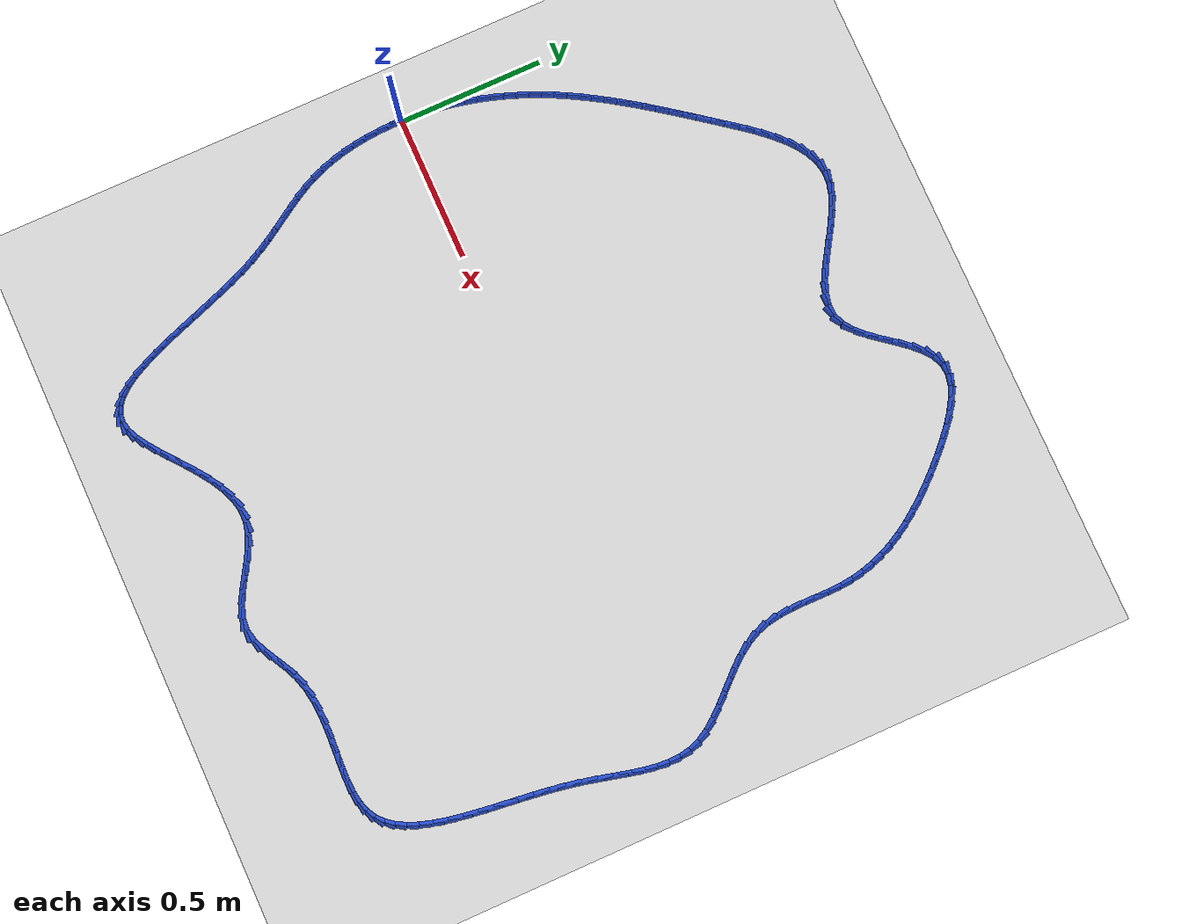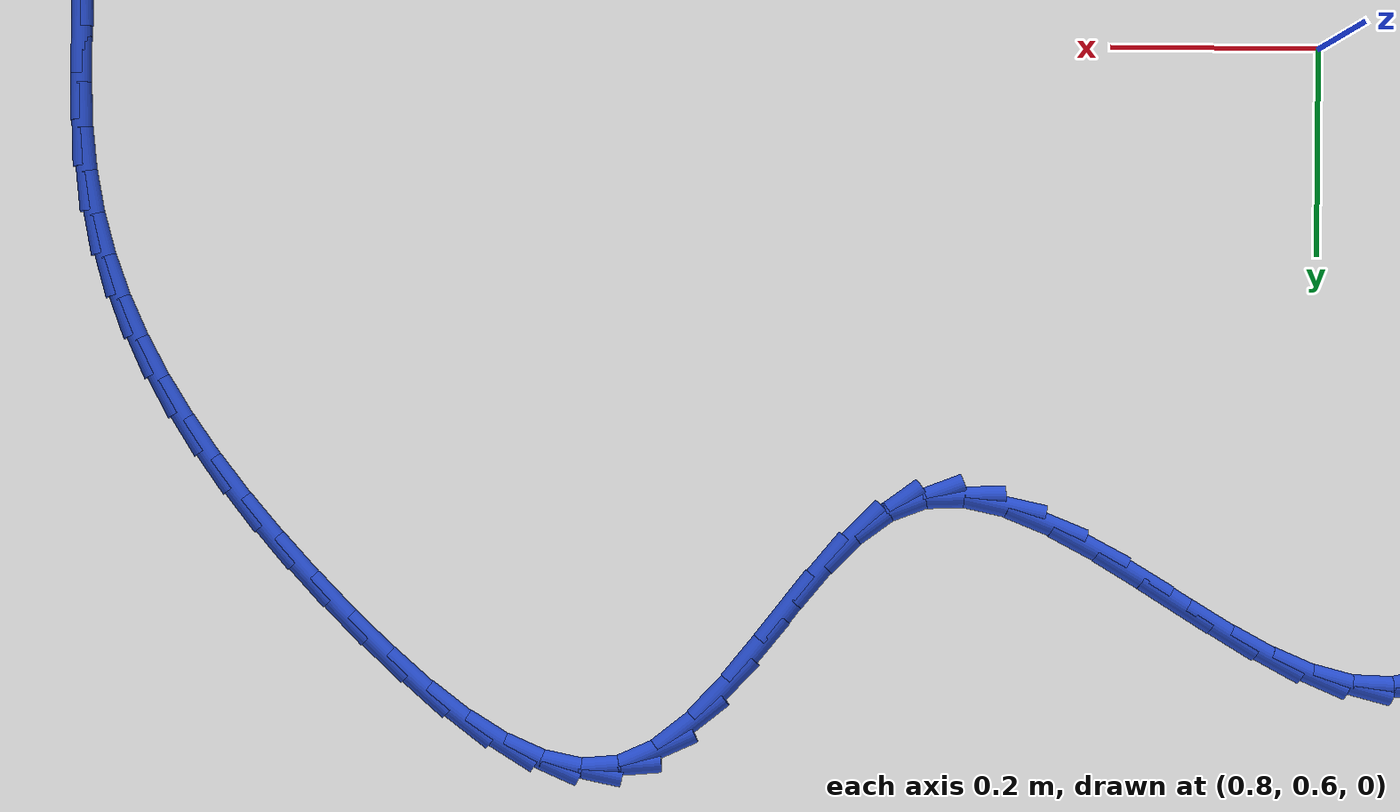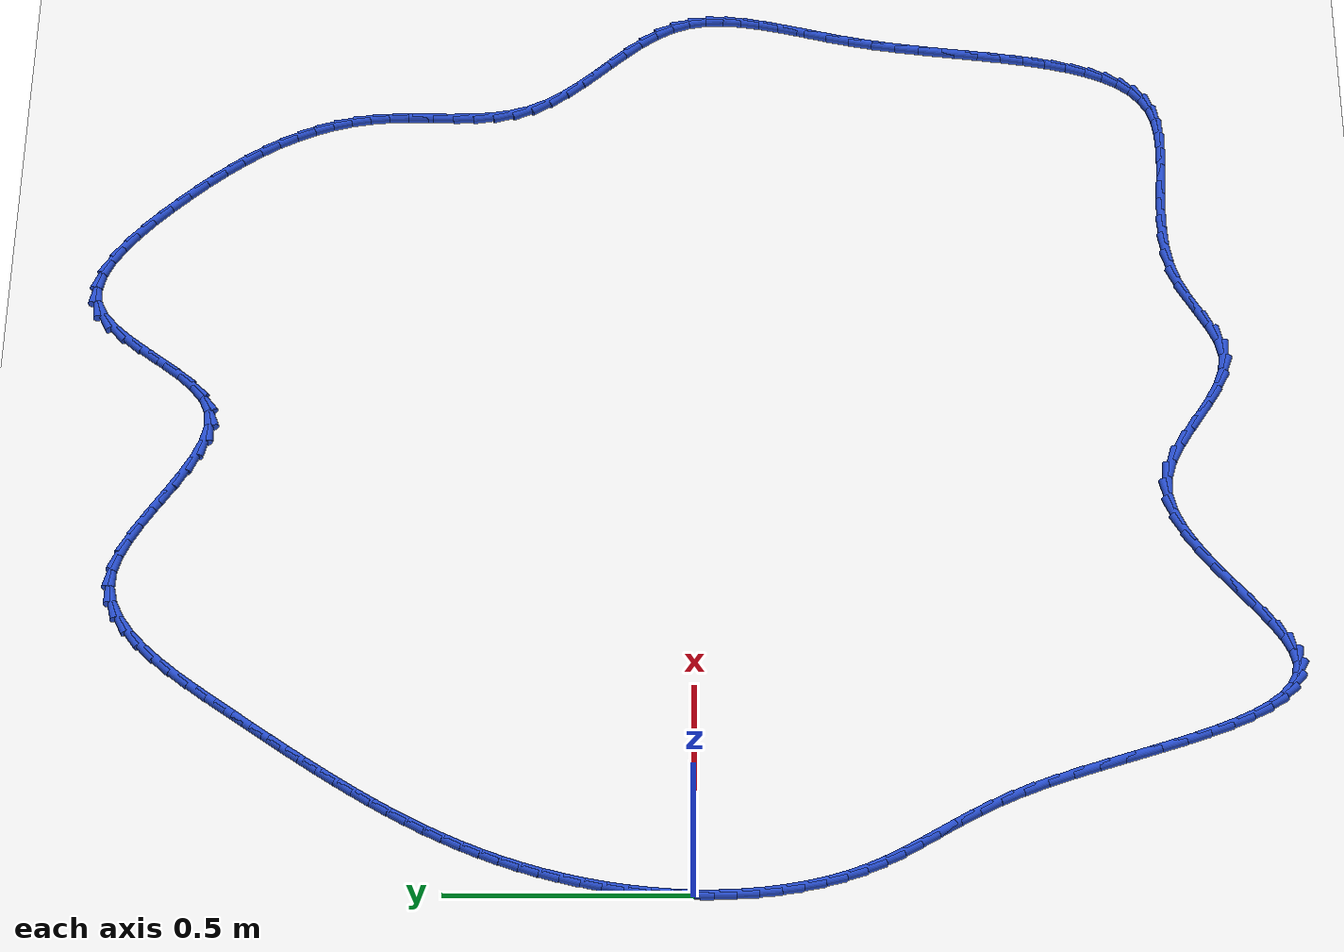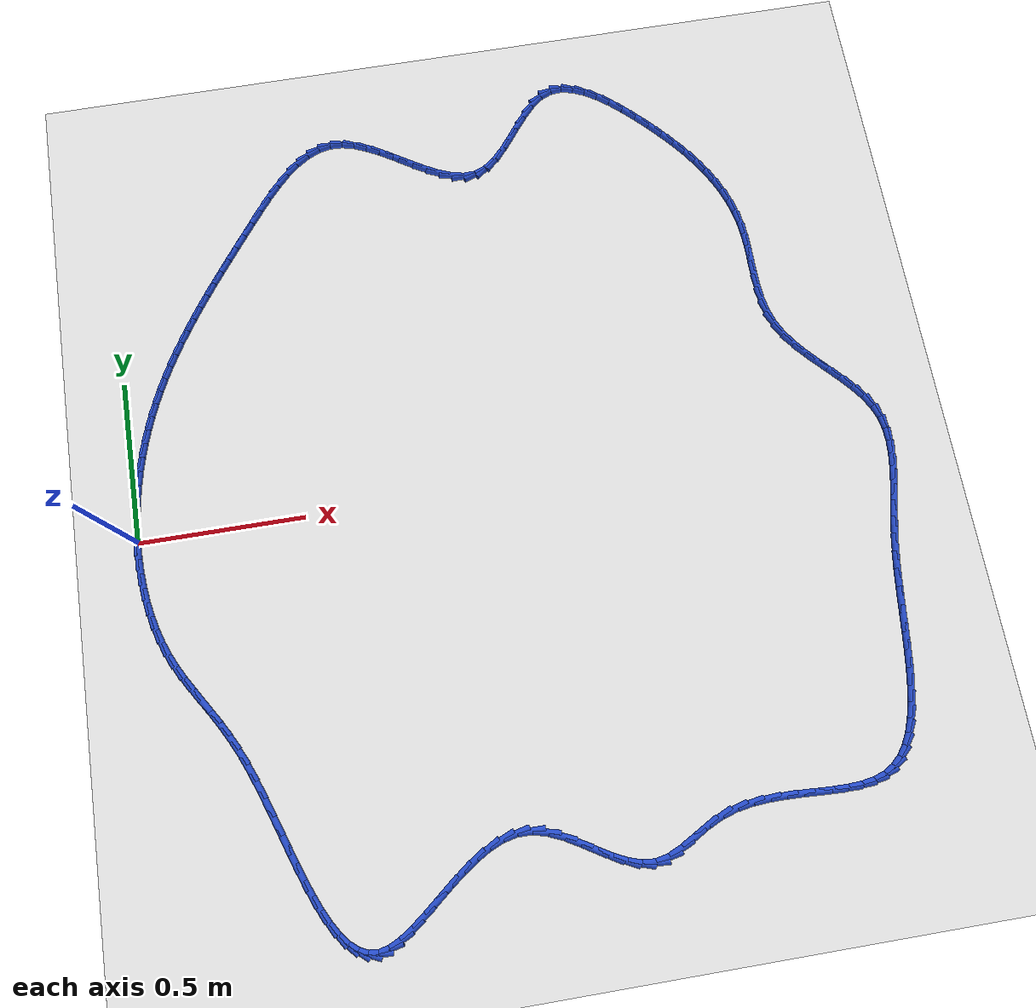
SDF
<sdf version="1.6">
 <world name="default">
  <light name="sun" type="directional">
   <pose>0 0 10 0 -0 0</pose>
   <diffuse>0.8 0.8 0.8 1</diffuse>
   <specular>0.2 0.2 0.2 1</specular>
   <attenuation>
    <range>1000</range>
    <constant>0.9</constant>
    <linear>0.01</linear>
    <quadratic>0.001</quadratic>
   </attenuation>
   <direction>-0.5 0.1 -0.9</direction>
  </light>
  <model name="ground_plane">
   <static>1</static>
   <link name="link">
    <collision name="collision">
     <geometry><plane><normal>0 0 1</normal><size>100 100</size></plane></geometry>
     <surface><friction><ode><mu>100</mu><mu2>50</mu2></ode></friction></surface>
    </collision>
    <visual name="visual">
     <cast_shadows>0</cast_shadows>
     <geometry><plane><normal>0 0 1</normal><size>100 100</size></plane></geometry>
     <material>
      <script><uri>file://media/materials/scripts/gazebo.material</uri><name>Gazebo/WhiteGlow</name></script>
     </material>
    </visual>
   </link>
  </model>
  <gravity>0 0 -9.8</gravity>
  <magnetic_field>6e-06 2.3e-05 -4.2e-05</magnetic_field>
  <atmosphere type="adiabatic"/>
  <physics name="default_physics" default="0" type="ode">
   <max_step_size>0.001</max_step_size>
   <real_time_factor>1</real_time_factor>
   <real_time_update_rate>1000</real_time_update_rate>
  </physics>
  <scene><ambient>0.4 0.4 0.4 1</ambient><background>0.7 0.7 0.7 1</background><shadows>1</shadows></scene>
  <spherical_coordinates>
   <surface_model>EARTH_WGS84</surface_model>
   <latitude_deg>0</latitude_deg>
   <longitude_deg>0</longitude_deg>
   <elevation>0</elevation>
   <heading_deg>0</heading_deg>
  </spherical_coordinates>
  <model name="line">
   <link name="link_0">
    <pose>2.42861286636753e-17 1.457167719820518e-16 0.01 0 1.57 1.531080158508508</pose>
    <collision name="collision">
     <geometry><cylinder><radius>0.01</radius><length>0.08</length></cylinder></geometry>
    </collision>
    <visual name="visual">
     <material>
      <script><name>Gazebo/Blue</name><uri>file://media/materials/scripts/gazebo.material</uri></script>
     </material>
     <geometry><cylinder><radius>0.01</radius><length>0.08</length></cylinder></geometry>
    </visual>
   </link>
   <link name="link_1">
    <pose>0.001789789169502115 0.04504080056214195 0.01 0 1.57 1.4895727189833496</pose>
    <collision name="collision">
     <geometry><cylinder><radius>0.01</radius><length>0.08</length></cylinder></geometry>
    </collision>
    <visual name="visual">
     <material>
      <script><name>Gazebo/Blue</name><uri>file://media/materials/scripts/gazebo.material</uri></script>
     </material>
     <geometry><cylinder><radius>0.01</radius><length>0.08</length></cylinder></geometry>
    </visual>
   </link>
   <link name="link_2">
    <pose>0.005428026617422109 0.08973511059844634 0.01 0 1.57 1.4492588038348522</pose>
    <collision name="collision">
     <geometry><cylinder><radius>0.01</radius><length>0.08</length></cylinder></geometry>
    </collision>
    <visual name="visual">
     <material>
      <script><name>Gazebo/Blue</name><uri>file://media/materials/scripts/gazebo.material</uri></script>
     </material>
     <geometry><cylinder><radius>0.01</radius><length>0.08</length></cylinder></geometry>
    </visual>
   </link>
   <link name="link_3">
    <pose>0.010833899442178533 0.13399493310844862 0.01 0 1.57 1.4100301552491794</pose>
    <collision name="collision">
     <geometry><cylinder><radius>0.01</radius><length>0.08</length></cylinder></geometry>
    </collision>
    <visual name="visual">
     <material>
      <script><name>Gazebo/Blue</name><uri>file://media/materials/scripts/gazebo.material</uri></script>
     </material>
     <geometry><cylinder><radius>0.01</radius><length>0.08</length></cylinder></geometry>
    </visual>
   </link>
   <link name="link_4">
    <pose>0.017926594742189904 0.17773227109168405 0.01 0 1.57 1.371766287814006</pose>
    <collision name="collision">
     <geometry><cylinder><radius>0.01</radius><length>0.08</length></cylinder></geometry>
    </collision>
    <visual name="visual">
     <material>
      <script><name>Gazebo/Blue</name><uri>file://media/materials/scripts/gazebo.material</uri></script>
     </material>
     <geometry><cylinder><radius>0.01</radius><length>0.08</length></cylinder></geometry>
    </visual>
   </link>
   <link name="link_5">
    <pose>0.02662529961587474 0.22085912754768786 0.01 0 1.57 1.3343358180927007</pose>
    <collision name="collision">
     <geometry><cylinder><radius>0.01</radius><length>0.08</length></cylinder></geometry>
    </collision>
    <visual name="visual">
     <material>
      <script><name>Gazebo/Blue</name><uri>file://media/materials/scripts/gazebo.material</uri></script>
     </material>
     <geometry><cylinder><radius>0.01</radius><length>0.08</length></cylinder></geometry>
    </visual>
   </link>
   <link name="link_6">
    <pose>0.03684920116165155 0.2632875054759953 0.01 0 1.57 1.2975971799241293</pose>
    <collision name="collision">
     <geometry><cylinder><radius>0.01</radius><length>0.08</length></cylinder></geometry>
    </collision>
    <visual name="visual">
     <material>
      <script><name>Gazebo/Blue</name><uri>file://media/materials/scripts/gazebo.material</uri></script>
     </material>
     <geometry><cylinder><radius>0.01</radius><length>0.08</length></cylinder></geometry>
    </visual>
   </link>
   <link name="link_7">
    <pose>0.048517486477938895 0.3049294078761417 0.01 0 1.57 1.2613987756101461</pose>
    <collision name="collision">
     <geometry><cylinder><radius>0.01</radius><length>0.08</length></cylinder></geometry>
    </collision>
    <visual name="visual">
     <material>
      <script><name>Gazebo/Blue</name><uri>file://media/materials/scripts/gazebo.material</uri></script>
     </material>
     <geometry><cylinder><radius>0.01</radius><length>0.08</length></cylinder></geometry>
    </visual>
   </link>
   <link name="link_8">
    <pose>0.06154934842835679 0.34569686291029034 0.01 0 1.57 1.2257033828325472</pose>
    <collision name="collision">
     <geometry><cylinder><radius>0.01</radius><length>0.08</length></cylinder></geometry>
    </collision>
    <visual name="visual">
     <material>
      <script><name>Gazebo/Blue</name><uri>file://media/materials/scripts/gazebo.material</uri></script>
     </material>
     <geometry><cylinder><radius>0.01</radius><length>0.08</length></cylinder></geometry>
    </visual>
   </link>
   <link name="link_9">
    <pose>0.07587385214336027 0.3855449869443742 0.01 0 1.57 1.1909487412343198</pose>
    <collision name="collision">
     <geometry><cylinder><radius>0.01</radius><length>0.08</length></cylinder></geometry>
    </collision>
    <visual name="visual">
     <material>
      <script><name>Gazebo/Blue</name><uri>file://media/materials/scripts/gazebo.material</uri></script>
     </material>
     <geometry><cylinder><radius>0.01</radius><length>0.08</length></cylinder></geometry>
    </visual>
   </link>
   <link name="link_10">
    <pose>0.09145016946160522 0.4245602991922726 0.01 0 1.57 1.1575225053839593</pose>
    <collision name="collision">
     <geometry><cylinder><radius>0.01</radius><length>0.08</length></cylinder></geometry>
    </collision>
    <visual name="visual">
     <material>
      <script><name>Gazebo/Blue</name><uri>file://media/materials/scripts/gazebo.material</uri></script>
     </material>
     <geometry><cylinder><radius>0.01</radius><length>0.08</length></cylinder></geometry>
    </visual>
   </link>
   <link name="link_11">
    <pose>0.10824319095762662 0.46285427869330087 0.01 0 1.57 1.1257328218221974</pose>
    <collision name="collision">
     <geometry><cylinder><radius>0.01</radius><length>0.08</length></cylinder></geometry>
    </collision>
    <visual name="visual">
     <material>
      <script><name>Gazebo/Blue</name><uri>file://media/materials/scripts/gazebo.material</uri></script>
     </material>
     <geometry><cylinder><radius>0.01</radius><length>0.08</length></cylinder></geometry>
    </visual>
   </link>
   <link name="link_12">
    <pose>0.12621780720595926 0.5005384044867738 0.01 0 1.57 1.09584935270586</pose>
    <collision name="collision">
     <geometry><cylinder><radius>0.01</radius><length>0.08</length></cylinder></geometry>
    </collision>
    <visual name="visual">
     <material>
      <script><name>Gazebo/Blue</name><uri>file://media/materials/scripts/gazebo.material</uri></script>
     </material>
     <geometry><cylinder><radius>0.01</radius><length>0.08</length></cylinder></geometry>
    </visual>
   </link>
   <link name="link_13">
    <pose>0.14533890878113806 0.5377241556120066 0.01 0 1.57 1.0680969405776368</pose>
    <collision name="collision">
     <geometry><cylinder><radius>0.01</radius><length>0.08</length></cylinder></geometry>
    </collision>
    <visual name="visual">
     <material>
      <script><name>Gazebo/Blue</name><uri>file://media/materials/scripts/gazebo.material</uri></script>
     </material>
     <geometry><cylinder><radius>0.01</radius><length>0.08</length></cylinder></geometry>
    </visual>
   </link>
   <link name="link_14">
    <pose>0.16557138625769782 0.5745230111083144 0.01 0 1.57 1.042652330992362</pose>
    <collision name="collision">
     <geometry><cylinder><radius>0.01</radius><length>0.08</length></cylinder></geometry>
    </collision>
    <visual name="visual">
     <material>
      <script><name>Gazebo/Blue</name><uri>file://media/materials/scripts/gazebo.material</uri></script>
     </material>
     <geometry><cylinder><radius>0.01</radius><length>0.08</length></cylinder></geometry>
    </visual>
   </link>
   <link name="link_15">
    <pose>0.18688013021017347 0.611046450015012 0.01 0 1.57 1.0196437410248822</pose>
    <collision name="collision">
     <geometry><cylinder><radius>0.01</radius><length>0.08</length></cylinder></geometry>
    </collision>
    <visual name="visual">
     <material>
      <script><name>Gazebo/Blue</name><uri>file://media/materials/scripts/gazebo.material</uri></script>
     </material>
     <geometry><cylinder><radius>0.01</radius><length>0.08</length></cylinder></geometry>
    </visual>
   </link>
   <link name="link_16">
    <pose>0.20923003121309977 0.6474059513714147 0.01 0 1.57 0.9991528003072331</pose>
    <collision name="collision">
     <geometry><cylinder><radius>0.01</radius><length>0.08</length></cylinder></geometry>
    </collision>
    <visual name="visual">
     <material>
      <script><name>Gazebo/Blue</name><uri>file://media/materials/scripts/gazebo.material</uri></script>
     </material>
     <geometry><cylinder><radius>0.01</radius><length>0.08</length></cylinder></geometry>
    </visual>
   </link>
   <link name="link_17">
    <pose>0.23258597984101165 0.6837129942168374 0.01 0 1.57 0.9812182529761322</pose>
    <collision name="collision">
     <geometry><cylinder><radius>0.01</radius><length>0.08</length></cylinder></geometry>
    </collision>
    <visual name="visual">
     <material>
      <script><name>Gazebo/Blue</name><uri>file://media/materials/scripts/gazebo.material</uri></script>
     </material>
     <geometry><cylinder><radius>0.01</radius><length>0.08</length></cylinder></geometry>
    </visual>
   </link>
   <link name="link_18">
    <pose>0.25691286666844404 0.7200790575905953 0.01 0 1.57 0.9658407849082543</pose>
    <collision name="collision">
     <geometry><cylinder><radius>0.01</radius><length>0.08</length></cylinder></geometry>
    </collision>
    <visual name="visual">
     <material>
      <script><name>Gazebo/Blue</name><uri>file://media/materials/scripts/gazebo.material</uri></script>
     </material>
     <geometry><cylinder><radius>0.01</radius><length>0.08</length></cylinder></geometry>
    </visual>
   </link>
   <link name="link_19">
    <pose>0.28217558226993167 0.7566156205320035 0.01 0 1.57 0.9529884020396097</pose>
    <collision name="collision">
     <geometry><cylinder><radius>0.01</radius><length>0.08</length></cylinder></geometry>
    </collision>
    <visual name="visual">
     <material>
      <script><name>Gazebo/Blue</name><uri>file://media/materials/scripts/gazebo.material</uri></script>
     </material>
     <geometry><cylinder><radius>0.01</radius><length>0.08</length></cylinder></geometry>
    </visual>
   </link>
   <link name="link_20">
    <pose>0.30833901722000967 0.7934341620803772 0.01 0 1.57 0.9426018967775512</pose>
    <collision name="collision">
     <geometry><cylinder><radius>0.01</radius><length>0.08</length></cylinder></geometry>
    </collision>
    <visual name="visual">
     <material>
      <script><name>Gazebo/Blue</name><uri>file://media/materials/scripts/gazebo.material</uri></script>
     </material>
     <geometry><cylinder><radius>0.01</radius><length>0.08</length></cylinder></geometry>
    </visual>
   </link>
   <link name="link_21">
    <pose>0.33536806209321257 0.8306461612750311 0.01 0 1.57 0.9346000682512817</pose>
    <collision name="collision">
     <geometry><cylinder><radius>0.01</radius><length>0.08</length></cylinder></geometry>
    </collision>
    <visual name="visual">
     <material>
      <script><name>Gazebo/Blue</name><uri>file://media/materials/scripts/gazebo.material</uri></script>
     </material>
     <geometry><cylinder><radius>0.01</radius><length>0.08</length></cylinder></geometry>
    </visual>
   </link>
   <link name="link_22">
    <pose>0.36322760746407534 0.8683630971552806 0.01 0 1.57 0.9288844848578905</pose>
    <collision name="collision">
     <geometry><cylinder><radius>0.01</radius><length>0.08</length></cylinder></geometry>
    </collision>
    <visual name="visual">
     <material>
      <script><name>Gazebo/Blue</name><uri>file://media/materials/scripts/gazebo.material</uri></script>
     </material>
     <geometry><cylinder><radius>0.01</radius><length>0.08</length></cylinder></geometry>
    </visual>
   </link>
   <link name="link_23">
    <pose>0.39188254390713295 0.9066964487604403 0.01 0 1.57 0.9253436805285772</pose>
    <collision name="collision">
     <geometry><cylinder><radius>0.01</radius><length>0.08</length></cylinder></geometry>
    </collision>
    <visual name="visual">
     <material>
      <script><name>Gazebo/Blue</name><uri>file://media/materials/scripts/gazebo.material</uri></script>
     </material>
     <geometry><cylinder><radius>0.01</radius><length>0.08</length></cylinder></geometry>
    </visual>
   </link>
   <link name="link_24">
    <pose>0.42129776199692004 0.9457576951298254 0.01 0 1.57 0.9236142865631829</pose>
    <collision name="collision">
     <geometry><cylinder><radius>0.01</radius><length>0.08</length></cylinder></geometry>
    </collision>
    <visual name="visual">
     <material>
      <script><name>Gazebo/Blue</name><uri>file://media/materials/scripts/gazebo.material</uri></script>
     </material>
     <geometry><cylinder><radius>0.01</radius><length>0.08</length></cylinder></geometry>
    </visual>
   </link>
   <link name="link_25">
    <pose>0.4514396891358187 0.9856402396798823 0.01 0 1.57 0.9157863498045397</pose>
    <collision name="collision">
     <geometry><cylinder><radius>0.01</radius><length>0.08</length></cylinder></geometry>
    </collision>
    <visual name="visual">
     <material>
      <script><name>Gazebo/Blue</name><uri>file://media/materials/scripts/gazebo.material</uri></script>
     </material>
     <geometry><cylinder><radius>0.01</radius><length>0.08</length></cylinder></geometry>
    </visual>
   </link>
   <link name="link_26">
    <pose>0.48232487261150736 1.0258479935513685 0.01 0 1.57 0.8923401497189923</pose>
    <collision name="collision">
     <geometry><cylinder><radius>0.01</radius><length>0.08</length></cylinder></geometry>
    </collision>
    <visual name="visual">
     <material>
      <script><name>Gazebo/Blue</name><uri>file://media/materials/scripts/gazebo.material</uri></script>
     </material>
     <geometry><cylinder><radius>0.01</radius><length>0.08</length></cylinder></geometry>
    </visual>
   </link>
   <link name="link_27">
    <pose>0.5140298895935932 1.0651788177514845 0.01 0 1.57 0.8512650316113434</pose>
    <collision name="collision">
     <geometry><cylinder><radius>0.01</radius><length>0.08</length></cylinder></geometry>
    </collision>
    <visual name="visual">
     <material>
      <script><name>Gazebo/Blue</name><uri>file://media/materials/scripts/gazebo.material</uri></script>
     </material>
     <geometry><cylinder><radius>0.01</radius><length>0.08</length></cylinder></geometry>
    </visual>
   </link>
   <link name="link_28">
    <pose>0.5466348563264035 1.1023889479485451 0.01 0 1.57 0.7892634327585224</pose>
    <collision name="collision">
     <geometry><cylinder><radius>0.01</radius><length>0.08</length></cylinder></geometry>
    </collision>
    <visual name="visual">
     <material>
      <script><name>Gazebo/Blue</name><uri>file://media/materials/scripts/gazebo.material</uri></script>
     </material>
     <geometry><cylinder><radius>0.01</radius><length>0.08</length></cylinder></geometry>
    </visual>
   </link>
   <link name="link_29">
    <pose>0.5802198890542654 1.136234619810866 0.01 0 1.57 0.7009479614808152</pose>
    <collision name="collision">
     <geometry><cylinder><radius>0.01</radius><length>0.08</length></cylinder></geometry>
    </collision>
    <visual name="visual">
     <material>
      <script><name>Gazebo/Blue</name><uri>file://media/materials/scripts/gazebo.material</uri></script>
     </material>
     <geometry><cylinder><radius>0.01</radius><length>0.08</length></cylinder></geometry>
    </visual>
   </link>
   <link name="link_30">
    <pose>0.6148651040215054 1.1654720690067624 0.01 0 1.57 0.5788244821238404</pose>
    <collision name="collision">
     <geometry><cylinder><radius>0.01</radius><length>0.08</length></cylinder></geometry>
    </collision>
    <visual name="visual">
     <material>
      <script><name>Gazebo/Blue</name><uri>file://media/materials/scripts/gazebo.material</uri></script>
     </material>
     <geometry><cylinder><radius>0.01</radius><length>0.08</length></cylinder></geometry>
    </visual>
   </link>
   <link name="link_31">
    <pose>0.6506506174724509 1.188857531204549 0.01 0 1.57 0.41466766069196653</pose>
    <collision name="collision">
     <geometry><cylinder><radius>0.01</radius><length>0.08</length></cylinder></geometry>
    </collision>
    <visual name="visual">
     <material>
      <script><name>Gazebo/Blue</name><uri>file://media/materials/scripts/gazebo.material</uri></script>
     </material>
     <geometry><cylinder><radius>0.01</radius><length>0.08</length></cylinder></geometry>
    </visual>
   </link>
   <link name="link_32">
    <pose>0.6876565456514293 1.2051472420725422 0.01 0 1.57 0.20463675493655478</pose>
    <collision name="collision">
     <geometry><cylinder><radius>0.01</radius><length>0.08</length></cylinder></geometry>
    </collision>
    <visual name="visual">
     <material>
      <script><name>Gazebo/Blue</name><uri>file://media/materials/scripts/gazebo.material</uri></script>
     </material>
     <geometry><cylinder><radius>0.01</radius><length>0.08</length></cylinder></geometry>
    </visual>
   </link>
   <link name="link_33">
    <pose>0.7259630048027671 1.213097437279056 0.01 0 1.57 -0.03997633124455144</pose>
    <collision name="collision">
     <geometry><cylinder><radius>0.01</radius><length>0.08</length></cylinder></geometry>
    </collision>
    <visual name="visual">
     <material>
      <script><name>Gazebo/Blue</name><uri>file://media/materials/scripts/gazebo.material</uri></script>
     </material>
     <geometry><cylinder><radius>0.01</radius><length>0.08</length></cylinder></geometry>
    </visual>
   </link>
   <link name="link_34">
    <pose>0.7656444221677583 1.2115102742186303 0.01 0 1.57 -0.2588761442368474</pose>
    <collision name="collision">
     <geometry><cylinder><radius>0.01</radius><length>0.08</length></cylinder></geometry>
    </collision>
    <visual name="visual">
     <material>
      <script><name>Gazebo/Blue</name><uri>file://media/materials/scripts/gazebo.material</uri></script>
     </material>
     <geometry><cylinder><radius>0.01</radius><length>0.08</length></cylinder></geometry>
    </visual>
   </link>
   <link name="link_35">
    <pose>0.8065920394312351 1.2006665871160003 0.01 0 1.57 -0.40705937856297325</pose>
    <collision name="collision">
     <geometry><cylinder><radius>0.01</radius><length>0.08</length></cylinder></geometry>
    </collision>
    <visual name="visual">
     <material>
      <script><name>Gazebo/Blue</name><uri>file://media/materials/scripts/gazebo.material</uri></script>
     </material>
     <geometry><cylinder><radius>0.01</radius><length>0.08</length></cylinder></geometry>
    </visual>
   </link>
   <link name="link_36">
    <pose>0.8484790315245709 1.1826074486230036 0.01 0 1.57 -0.4985504513341427</pose>
    <collision name="collision">
     <geometry><cylinder><radius>0.01</radius><length>0.08</length></cylinder></geometry>
    </collision>
    <visual name="visual">
     <material>
      <script><name>Gazebo/Blue</name><uri>file://media/materials/scripts/gazebo.material</uri></script>
     </material>
     <geometry><cylinder><radius>0.01</radius><length>0.08</length></cylinder></geometry>
    </visual>
   </link>
   <link name="link_37">
    <pose>0.8909658416292742 1.1594767022861783 0.01 0 1.57 -0.5474466636740964</pose>
    <collision name="collision">
     <geometry><cylinder><radius>0.01</radius><length>0.08</length></cylinder></geometry>
    </collision>
    <visual name="visual">
     <material>
      <script><name>Gazebo/Blue</name><uri>file://media/materials/scripts/gazebo.material</uri></script>
     </material>
     <geometry><cylinder><radius>0.01</radius><length>0.08</length></cylinder></geometry>
    </visual>
   </link>
   <link name="link_38">
    <pose>0.9337129129268529 1.1334181916520631 0.01 0 1.57 -0.5615444437678313</pose>
    <collision name="collision">
     <geometry><cylinder><radius>0.01</radius><length>0.08</length></cylinder></geometry>
    </collision>
    <visual name="visual">
     <material>
      <script><name>Gazebo/Blue</name><uri>file://media/materials/scripts/gazebo.material</uri></script>
     </material>
     <geometry><cylinder><radius>0.01</radius><length>0.08</length></cylinder></geometry>
    </visual>
   </link>
   <link name="link_39">
    <pose>0.9763806885988158 1.1065757602671966 0.01 0 1.57 -0.5427336826077157</pose>
    <collision name="collision">
     <geometry><cylinder><radius>0.01</radius><length>0.08</length></cylinder></geometry>
    </collision>
    <visual name="visual">
     <material>
      <script><name>Gazebo/Blue</name><uri>file://media/materials/scripts/gazebo.material</uri></script>
     </material>
     <geometry><cylinder><radius>0.01</radius><length>0.08</length></cylinder></geometry>
    </visual>
   </link>
   <link name="link_40">
    <pose>1.018629611826671 1.0810932516781164 0.01 0 1.57 -0.4871472450354404</pose>
    <collision name="collision">
     <geometry><cylinder><radius>0.01</radius><length>0.08</length></cylinder></geometry>
    </collision>
    <visual name="visual">
     <material>
      <script><name>Gazebo/Blue</name><uri>file://media/materials/scripts/gazebo.material</uri></script>
     </material>
     <geometry><cylinder><radius>0.01</radius><length>0.08</length></cylinder></geometry>
    </visual>
   </link>
   <link name="link_41">
    <pose>1.0601201257919268 1.059114509431361 0.01 0 1.57 -0.38421681722168144</pose>
    <collision name="collision">
     <geometry><cylinder><radius>0.01</radius><length>0.08</length></cylinder></geometry>
    </collision>
    <visual name="visual">
     <material>
      <script><name>Gazebo/Blue</name><uri>file://media/materials/scripts/gazebo.material</uri></script>
     </material>
     <geometry><cylinder><radius>0.01</radius><length>0.08</length></cylinder></geometry>
    </visual>
   </link>
   <link name="link_42">
    <pose>1.1005126736760915 1.0427833770734682 0.01 0 1.57 -0.21580517220610754</pose>
    <collision name="collision">
     <geometry><cylinder><radius>0.01</radius><length>0.08</length></cylinder></geometry>
    </collision>
    <visual name="visual">
     <material>
      <script><name>Gazebo/Blue</name><uri>file://media/materials/scripts/gazebo.material</uri></script>
     </material>
     <geometry><cylinder><radius>0.01</radius><length>0.08</length></cylinder></geometry>
    </visual>
   </link>
   <link name="link_43">
    <pose>1.1394676986606738 1.034243698150977 0.01 0 1.57 0.037521252191220794</pose>
    <collision name="collision">
     <geometry><cylinder><radius>0.01</radius><length>0.08</length></cylinder></geometry>
    </collision>
    <visual name="visual">
     <material>
      <script><name>Gazebo/Blue</name><uri>file://media/materials/scripts/gazebo.material</uri></script>
     </material>
     <geometry><cylinder><radius>0.01</radius><length>0.08</length></cylinder></geometry>
    </visual>
   </link>
   <link name="link_44">
    <pose>1.1766456439271813 1.0356393162104254 0.01 0 1.57 0.36178900563334204</pose>
    <collision name="collision">
     <geometry><cylinder><radius>0.01</radius><length>0.08</length></cylinder></geometry>
    </collision>
    <visual name="visual">
     <material>
      <script><name>Gazebo/Blue</name><uri>file://media/materials/scripts/gazebo.material</uri></script>
     </material>
     <geometry><cylinder><radius>0.01</radius><length>0.08</length></cylinder></geometry>
    </visual>
   </link>
   <link name="link_45">
    <pose>1.211739344616086 1.0489204114436608 0.01 0 1.57 0.6319163065744884</pose>
    <collision name="collision">
     <geometry><cylinder><radius>0.01</radius><length>0.08</length></cylinder></geometry>
    </collision>
    <visual name="visual">
     <material>
      <script><name>Gazebo/Blue</name><uri>file://media/materials/scripts/gazebo.material</uri></script>
     </material>
     <geometry><cylinder><radius>0.01</radius><length>0.08</length></cylinder></geometry>
    </visual>
   </link>
   <link name="link_46">
    <pose>1.2449150388757368 1.0732068068316694 0.01 0 1.57 0.7929548387686479</pose>
    <collision name="collision">
     <geometry><cylinder><radius>0.01</radius><length>0.08</length></cylinder></geometry>
    </collision>
    <visual name="visual">
     <material>
      <script><name>Gazebo/Blue</name><uri>file://media/materials/scripts/gazebo.material</uri></script>
     </material>
     <geometry><cylinder><radius>0.01</radius><length>0.08</length></cylinder></geometry>
    </visual>
   </link>
   <link name="link_47">
    <pose>1.2766977087510347 1.1054734860587563 0.01 0 1.57 0.876858586726603</pose>
    <collision name="collision">
     <geometry><cylinder><radius>0.01</radius><length>0.08</length></cylinder></geometry>
    </collision>
    <visual name="visual">
     <material>
      <script><name>Gazebo/Blue</name><uri>file://media/materials/scripts/gazebo.material</uri></script>
     </material>
     <geometry><cylinder><radius>0.01</radius><length>0.08</length></cylinder></geometry>
    </visual>
   </link>
   <link name="link_48">
    <pose>1.3076212420772027 1.14264218733458 0.01 0 1.57 0.9054402420533546</pose>
    <collision name="collision">
     <geometry><cylinder><radius>0.01</radius><length>0.08</length></cylinder></geometry>
    </collision>
    <visual name="visual">
     <material>
      <script><name>Gazebo/Blue</name><uri>file://media/materials/scripts/gazebo.material</uri></script>
     </material>
     <geometry><cylinder><radius>0.01</radius><length>0.08</length></cylinder></geometry>
    </visual>
   </link>
   <link name="link_49">
    <pose>1.338219526689463 1.181634648868799 0.01 0 1.57 0.8861723919869269</pose>
    <collision name="collision">
     <geometry><cylinder><radius>0.01</radius><length>0.08</length></cylinder></geometry>
    </collision>
    <visual name="visual">
     <material>
      <script><name>Gazebo/Blue</name><uri>file://media/materials/scripts/gazebo.material</uri></script>
     </material>
     <geometry><cylinder><radius>0.01</radius><length>0.08</length></cylinder></geometry>
    </visual>
   </link>
   <link name="link_50">
    <pose>1.3690264504230378 1.2193726088710704 0.01 0 1.57 0.8139602663758612</pose>
    <collision name="collision">
     <geometry><cylinder><radius>0.01</radius><length>0.08</length></cylinder></geometry>
    </collision>
    <visual name="visual">
     <material>
      <script><name>Gazebo/Blue</name><uri>file://media/materials/scripts/gazebo.material</uri></script>
     </material>
     <geometry><cylinder><radius>0.01</radius><length>0.08</length></cylinder></geometry>
    </visual>
   </link>
   <link name="link_51">
    <pose>1.40057590111315 1.2527778055510532 0.01 0 1.57 0.6697705460041684</pose>
    <collision name="collision">
     <geometry><cylinder><radius>0.01</radius><length>0.08</length></cylinder></geometry>
    </collision>
    <visual name="visual">
     <material>
      <script><name>Gazebo/Blue</name><uri>file://media/materials/scripts/gazebo.material</uri></script>
     </material>
     <geometry><cylinder><radius>0.01</radius><length>0.08</length></cylinder></geometry>
    </visual>
   </link>
   <link name="link_52">
    <pose>1.433401766595023 1.2787719771184067 0.01 0 1.57 0.4209304914450919</pose>
    <collision name="collision">
     <geometry><cylinder><radius>0.01</radius><length>0.08</length></cylinder></geometry>
    </collision>
    <visual name="visual">
     <material>
      <script><name>Gazebo/Blue</name><uri>file://media/materials/scripts/gazebo.material</uri></script>
     </material>
     <geometry><cylinder><radius>0.01</radius><length>0.08</length></cylinder></geometry>
    </visual>
   </link>
   <link name="link_53">
    <pose>1.4680376519331941 1.2942780843155677 0.01 0 1.57 0.08339045549027199</pose>
    <collision name="collision">
     <geometry><cylinder><radius>0.01</radius><length>0.08</length></cylinder></geometry>
    </collision>
    <visual name="visual">
     <material>
      <script><name>Gazebo/Blue</name><uri>file://media/materials/scripts/gazebo.material</uri></script>
     </material>
     <geometry><cylinder><radius>0.01</radius><length>0.08</length></cylinder></geometry>
    </visual>
   </link>
   <link name="link_54">
    <pose>1.5047562352820636 1.297347181140041 0.01 0 1.57 -0.20830182374918246</pose>
    <collision name="collision">
     <geometry><cylinder><radius>0.01</radius><length>0.08</length></cylinder></geometry>
    </collision>
    <visual name="visual">
     <material>
      <script><name>Gazebo/Blue</name><uri>file://media/materials/scripts/gazebo.material</uri></script>
     </material>
     <geometry><cylinder><radius>0.01</radius><length>0.08</length></cylinder></geometry>
    </visual>
   </link>
   <link name="link_55">
    <pose>1.5430865530261562 1.2892453876947545 0.01 0 1.57 -0.41723393961143784</pose>
    <collision name="collision">
     <geometry><cylinder><radius>0.01</radius><length>0.08</length></cylinder></geometry>
    </collision>
    <visual name="visual">
     <material>
      <script><name>Gazebo/Blue</name><uri>file://media/materials/scripts/gazebo.material</uri></script>
     </material>
     <geometry><cylinder><radius>0.01</radius><length>0.08</length></cylinder></geometry>
    </visual>
   </link>
   <link name="link_56">
    <pose>1.582426035590428 1.2718078102222146 0.01 0 1.57 -0.5603515685283387</pose>
    <collision name="collision">
     <geometry><cylinder><radius>0.01</radius><length>0.08</length></cylinder></geometry>
    </collision>
    <visual name="visual">
     <material>
      <script><name>Gazebo/Blue</name><uri>file://media/materials/scripts/gazebo.material</uri></script>
     </material>
     <geometry><cylinder><radius>0.01</radius><length>0.08</length></cylinder></geometry>
    </visual>
   </link>
   <link name="link_57">
    <pose>1.6221721133998386 1.2468695549649291 0.01 0 1.57 -0.6585592411189238</pose>
    <collision name="collision">
     <geometry><cylinder><radius>0.01</radius><length>0.08</length></cylinder></geometry>
    </collision>
    <visual name="visual">
     <material>
      <script><name>Gazebo/Blue</name><uri>file://media/materials/scripts/gazebo.material</uri></script>
     </material>
     <geometry><cylinder><radius>0.01</radius><length>0.08</length></cylinder></geometry>
    </visual>
   </link>
   <link name="link_58">
    <pose>1.661722216879345 1.2162657281654035 0.01 0 1.57 -0.7264759816325205</pose>
    <collision name="collision">
     <geometry><cylinder><radius>0.01</radius><length>0.08</length></cylinder></geometry>
    </collision>
    <visual name="visual">
     <material>
      <script><name>Gazebo/Blue</name><uri>file://media/materials/scripts/gazebo.material</uri></script>
     </material>
     <geometry><cylinder><radius>0.01</radius><length>0.08</length></cylinder></geometry>
    </visual>
   </link>
   <link name="link_59">
    <pose>1.7004737764539055 1.1818314360661455 0.01 0 1.57 -0.7729185493805275</pose>
    <collision name="collision">
     <geometry><cylinder><radius>0.01</radius><length>0.08</length></cylinder></geometry>
    </collision>
    <visual name="visual">
     <material>
      <script><name>Gazebo/Blue</name><uri>file://media/materials/scripts/gazebo.material</uri></script>
     </material>
     <geometry><cylinder><radius>0.01</radius><length>0.08</length></cylinder></geometry>
    </visual>
   </link>
   <link name="link_60">
    <pose>1.7378242225484788 1.1454017849096623 0.01 0 1.57 -0.8042346697236329</pose>
    <collision name="collision">
     <geometry><cylinder><radius>0.01</radius><length>0.08</length></cylinder></geometry>
    </collision>
    <visual name="visual">
     <material>
      <script><name>Gazebo/Blue</name><uri>file://media/materials/scripts/gazebo.material</uri></script>
     </material>
     <geometry><cylinder><radius>0.01</radius><length>0.08</length></cylinder></geometry>
    </visual>
   </link>
   <link name="link_61">
    <pose>1.77320855345801 1.1086586640896534 0.01 0 1.57 -0.8348037902321448</pose>
    <collision name="collision">
     <geometry><cylinder><radius>0.01</radius><length>0.08</length></cylinder></geometry>
    </collision>
    <visual name="visual">
     <material>
      <script><name>Gazebo/Blue</name><uri>file://media/materials/scripts/gazebo.material</uri></script>
     </material>
     <geometry><cylinder><radius>0.01</radius><length>0.08</length></cylinder></geometry>
    </visual>
   </link>
   <link name="link_62">
    <pose>1.8063631513342844 1.0720547986942388 0.01 0 1.57 -0.8711824764554376</pose>
    <collision name="collision">
     <geometry><cylinder><radius>0.01</radius><length>0.08</length></cylinder></geometry>
    </collision>
    <visual name="visual">
     <material>
      <script><name>Gazebo/Blue</name><uri>file://media/materials/scripts/gazebo.material</uri></script>
     </material>
     <geometry><cylinder><radius>0.01</radius><length>0.08</length></cylinder></geometry>
    </visual>
   </link>
   <link name="link_63">
    <pose>1.8371693598200889 1.0354517026820103 0.01 0 1.57 -0.913819224097749</pose>
    <collision name="collision">
     <geometry><cylinder><radius>0.01</radius><length>0.08</length></cylinder></geometry>
    </collision>
    <visual name="visual">
     <material>
      <script><name>Gazebo/Blue</name><uri>file://media/materials/scripts/gazebo.material</uri></script>
     </material>
     <geometry><cylinder><radius>0.01</radius><length>0.08</length></cylinder></geometry>
    </visual>
   </link>
   <link name="link_64">
    <pose>1.8655094468915325 0.9987071202093563 0.01 0 1.57 -0.9630416682131838</pose>
    <collision name="collision">
     <geometry><cylinder><radius>0.01</radius><length>0.08</length></cylinder></geometry>
    </collision>
    <visual name="visual">
     <material>
      <script><name>Gazebo/Blue</name><uri>file://media/materials/scripts/gazebo.material</uri></script>
     </material>
     <geometry><cylinder><radius>0.01</radius><length>0.08</length></cylinder></geometry>
    </visual>
   </link>
   <link name="link_65">
    <pose>1.8912656805247259 0.9616787954326654 0.01 0 1.57 -1.019028372528602</pose>
    <collision name="collision">
     <geometry><cylinder><radius>0.01</radius><length>0.08</length></cylinder></geometry>
    </collision>
    <visual name="visual">
     <material>
      <script><name>Gazebo/Blue</name><uri>file://media/materials/scripts/gazebo.material</uri></script>
     </material>
     <geometry><cylinder><radius>0.01</radius><length>0.08</length></cylinder></geometry>
    </visual>
   </link>
   <link name="link_66">
    <pose>1.9143203286957788 0.9242244725083255 0.01 0 1.57 -1.0817276046815947</pose>
    <collision name="collision">
     <geometry><cylinder><radius>0.01</radius><length>0.08</length></cylinder></geometry>
    </collision>
    <visual name="visual">
     <material>
      <script><name>Gazebo/Blue</name><uri>file://media/materials/scripts/gazebo.material</uri></script>
     </material>
     <geometry><cylinder><radius>0.01</radius><length>0.08</length></cylinder></geometry>
    </visual>
   </link>
   <link name="link_67">
    <pose>1.934555659380802 0.8862018955927263 0.01 0 1.57 -1.1507716163277262</pose>
    <collision name="collision">
     <geometry><cylinder><radius>0.01</radius><length>0.08</length></cylinder></geometry>
    </collision>
    <visual name="visual">
     <material>
      <script><name>Gazebo/Blue</name><uri>file://media/materials/scripts/gazebo.material</uri></script>
     </material>
     <geometry><cylinder><radius>0.01</radius><length>0.08</length></cylinder></geometry>
    </visual>
   </link>
   <link name="link_68">
    <pose>1.9518539405559046 0.8474688088422552 0.01 0 1.57 -1.225406406048052</pose>
    <collision name="collision">
     <geometry><cylinder><radius>0.01</radius><length>0.08</length></cylinder></geometry>
    </collision>
    <visual name="visual">
     <material>
      <script><name>Gazebo/Blue</name><uri>file://media/materials/scripts/gazebo.material</uri></script>
     </material>
     <geometry><cylinder><radius>0.01</radius><length>0.08</length></cylinder></geometry>
    </visual>
   </link>
   <link name="link_69">
    <pose>1.9660974401971967 0.8078829564133001 0.01 0 1.57 -1.3044645760982947</pose>
    <collision name="collision">
     <geometry><cylinder><radius>0.01</radius><length>0.08</length></cylinder></geometry>
    </collision>
    <visual name="visual">
     <material>
      <script><name>Gazebo/Blue</name><uri>file://media/materials/scripts/gazebo.material</uri></script>
     </material>
     <geometry><cylinder><radius>0.01</radius><length>0.08</length></cylinder></geometry>
    </visual>
   </link>
   <link name="link_70">
    <pose>1.977168426280788 0.7673020824622507 0.01 0 1.57 -1.386407517514661</pose>
    <collision name="collision">
     <geometry><cylinder><radius>0.01</radius><length>0.08</length></cylinder></geometry>
    </collision>
    <visual name="visual">
     <material>
      <script><name>Gazebo/Blue</name><uri>file://media/materials/scripts/gazebo.material</uri></script>
     </material>
     <geometry><cylinder><radius>0.01</radius><length>0.08</length></cylinder></geometry>
    </visual>
   </link>
   <link name="link_71">
    <pose>1.9849491667827892 0.7255839311454947 0.01 0 1.57 -1.4691746983548502</pose>
    <collision name="collision">
     <geometry><cylinder><radius>0.01</radius><length>0.08</length></cylinder></geometry>
    </collision>
    <visual name="visual">
     <material>
      <script><name>Gazebo/Blue</name><uri>file://media/materials/scripts/gazebo.material</uri></script>
     </material>
     <geometry><cylinder><radius>0.01</radius><length>0.08</length></cylinder></geometry>
    </visual>
   </link>
   <link name="link_72">
    <pose>1.989333277671337 0.6825910264891865 0.01 0 1.57 -1.5377014814712118</pose>
    <collision name="collision">
     <geometry><cylinder><radius>0.01</radius><length>0.08</length></cylinder></geometry>
    </collision>
    <visual name="visual">
     <material>
      <script><name>Gazebo/Blue</name><uri>file://media/materials/scripts/gazebo.material</uri></script>
     </material>
     <geometry><cylinder><radius>0.01</radius><length>0.08</length></cylinder></geometry>
    </visual>
   </link>
   <link name="link_73">
    <pose>1.9907952945976548 0.6384305807799963 0.01 0 1.57 1.5677131679715255</pose>
    <collision name="collision">
     <geometry><cylinder><radius>0.01</radius><length>0.08</length></cylinder></geometry>
    </collision>
    <visual name="visual">
     <material>
      <script><name>Gazebo/Blue</name><uri>file://media/materials/scripts/gazebo.material</uri></script>
     </material>
     <geometry><cylinder><radius>0.01</radius><length>0.08</length></cylinder></geometry>
    </visual>
   </link>
   <link name="link_74">
    <pose>1.9906569715717344 0.5935666618089253 0.01 0 1.57 1.5630336068367423</pose>
    <collision name="collision">
     <geometry><cylinder><radius>0.01</radius><length>0.08</length></cylinder></geometry>
    </collision>
    <visual name="visual">
     <material>
      <script><name>Gazebo/Blue</name><uri>file://media/materials/scripts/gazebo.material</uri></script>
     </material>
     <geometry><cylinder><radius>0.01</radius><length>0.08</length></cylinder></geometry>
    </visual>
   </link>
   <link name="link_75">
    <pose>1.9903070591263987 0.5484915568663487 0.01 0 1.57 -1.5523305819873974</pose>
    <collision name="collision">
     <geometry><cylinder><radius>0.01</radius><length>0.08</length></cylinder></geometry>
    </collision>
    <visual name="visual">
     <material>
      <script><name>Gazebo/Blue</name><uri>file://media/materials/scripts/gazebo.material</uri></script>
     </material>
     <geometry><cylinder><radius>0.01</radius><length>0.08</length></cylinder></geometry>
    </visual>
   </link>
   <link name="link_76">
    <pose>1.9911343077944703 0.5036975532426408 0.01 0 1.57 -1.4938672787153076</pose>
    <collision name="collision">
     <geometry><cylinder><radius>0.01</radius><length>0.08</length></cylinder></geometry>
    </collision>
    <visual name="visual">
     <material>
      <script><name>Gazebo/Blue</name><uri>file://media/materials/scripts/gazebo.material</uri></script>
     </material>
     <geometry><cylinder><radius>0.01</radius><length>0.08</length></cylinder></geometry>
    </visual>
   </link>
   <link name="link_77">
    <pose>1.9945274681087735 0.45967693822817557 0.01 0 1.57 -1.400599910378376</pose>
    <collision name="collision">
     <geometry><cylinder><radius>0.01</radius><length>0.08</length></cylinder></geometry>
    </collision>
    <visual name="visual">
     <material>
      <script><name>Gazebo/Blue</name><uri>file://media/materials/scripts/gazebo.material</uri></script>
     </material>
     <geometry><cylinder><radius>0.01</radius><length>0.08</length></cylinder></geometry>
    </visual>
   </link>
   <link name="link_78">
    <pose>2.001875290602131 0.41692199911332845 0.01 0 1.57 -1.270587425750175</pose>
    <collision name="collision">
     <geometry><cylinder><radius>0.01</radius><length>0.08</length></cylinder></geometry>
    </collision>
    <visual name="visual">
     <material>
      <script><name>Gazebo/Blue</name><uri>file://media/materials/scripts/gazebo.material</uri></script>
     </material>
     <geometry><cylinder><radius>0.01</radius><length>0.08</length></cylinder></geometry>
    </visual>
   </link>
   <link name="link_79">
    <pose>2.014566525807367 0.37592502318847354 0.01 0 1.57 -1.1155342573622817</pose>
    <collision name="collision">
     <geometry><cylinder><radius>0.01</radius><length>0.08</length></cylinder></geometry>
    </collision>
    <visual name="visual">
     <material>
      <script><name>Gazebo/Blue</name><uri>file://media/materials/scripts/gazebo.material</uri></script>
     </material>
     <geometry><cylinder><radius>0.01</radius><length>0.08</length></cylinder></geometry>
    </visual>
   </link>
   <link name="link_80">
    <pose>2.0335958968409886 0.33705479488190176 0.01 0 1.57 -0.9866766034194904</pose>
    <collision name="collision">
     <geometry><cylinder><radius>0.01</radius><length>0.08</length></cylinder></geometry>
    </collision>
    <visual name="visual">
     <material>
      <script><name>Gazebo/Blue</name><uri>file://media/materials/scripts/gazebo.material</uri></script>
     </material>
     <geometry><cylinder><radius>0.01</radius><length>0.08</length></cylinder></geometry>
    </visual>
   </link>
   <link name="link_81">
    <pose>2.058039713170704 0.3000787963610054 0.01 0 1.57 -0.896846586519787</pose>
    <collision name="collision">
     <geometry><cylinder><radius>0.01</radius><length>0.08</length></cylinder></geometry>
    </collision>
    <visual name="visual">
     <material>
      <script><name>Gazebo/Blue</name><uri>file://media/materials/scripts/gazebo.material</uri></script>
     </material>
     <geometry><cylinder><radius>0.01</radius><length>0.08</length></cylinder></geometry>
    </visual>
   </link>
   <link name="link_82">
    <pose>2.08639129586091 0.264581779522668 0.01 0 1.57 -0.8418043457936921</pose>
    <collision name="collision">
     <geometry><cylinder><radius>0.01</radius><length>0.08</length></cylinder></geometry>
    </collision>
    <visual name="visual">
     <material>
      <script><name>Gazebo/Blue</name><uri>file://media/materials/scripts/gazebo.material</uri></script>
     </material>
     <geometry><cylinder><radius>0.01</radius><length>0.08</length></cylinder></geometry>
    </visual>
   </link>
   <link name="link_83">
    <pose>2.1171438312799236 0.23014845404500847 0.01 0 1.57 -0.8180657013874502</pose>
    <collision name="collision">
     <geometry><cylinder><radius>0.01</radius><length>0.08</length></cylinder></geometry>
    </collision>
    <visual name="visual">
     <material>
      <script><name>Gazebo/Blue</name><uri>file://media/materials/scripts/gazebo.material</uri></script>
     </material>
     <geometry><cylinder><radius>0.01</radius><length>0.08</length></cylinder></geometry>
    </visual>
   </link>
   <link name="link_84">
    <pose>2.1487905057960646 0.19636352960614678 0.01 0 1.57 -0.8243624385701178</pose>
    <collision name="collision">
     <geometry><cylinder><radius>0.01</radius><length>0.08</length></cylinder></geometry>
    </collision>
    <visual name="visual">
     <material>
      <script><name>Gazebo/Blue</name><uri>file://media/materials/scripts/gazebo.material</uri></script>
     </material>
     <geometry><cylinder><radius>0.01</radius><length>0.08</length></cylinder></geometry>
    </visual>
   </link>
   <link name="link_85">
    <pose>2.1798245057776517 0.16281171588420157 0.01 0 1.57 -0.8621758581553646</pose>
    <collision name="collision">
     <geometry><cylinder><radius>0.01</radius><length>0.08</length></cylinder></geometry>
    </collision>
    <visual name="visual">
     <material>
      <script><name>Gazebo/Blue</name><uri>file://media/materials/scripts/gazebo.material</uri></script>
     </material>
     <geometry><cylinder><radius>0.01</radius><length>0.08</length></cylinder></geometry>
    </visual>
   </link>
   <link name="link_86">
    <pose>2.2087390175930066 0.12907772255729272 0.01 0 1.57 -0.9359330514738584</pose>
    <collision name="collision">
     <geometry><cylinder><radius>0.01</radius><length>0.08</length></cylinder></geometry>
    </collision>
    <visual name="visual">
     <material>
      <script><name>Gazebo/Blue</name><uri>file://media/materials/scripts/gazebo.material</uri></script>
     </material>
     <geometry><cylinder><radius>0.01</radius><length>0.08</length></cylinder></geometry>
    </visual>
   </link>
   <link name="link_87">
    <pose>2.2340272276104463 0.09474625930353911 0.01 0 1.57 -1.052538033385519</pose>
    <collision name="collision">
     <geometry><cylinder><radius>0.01</radius><length>0.08</length></cylinder></geometry>
    </collision>
    <visual name="visual">
     <material>
      <script><name>Gazebo/Blue</name><uri>file://media/materials/scripts/gazebo.material</uri></script>
     </material>
     <geometry><cylinder><radius>0.01</radius><length>0.08</length></cylinder></geometry>
    </visual>
   </link>
   <link name="link_88">
    <pose>2.254182322198291 0.05940203580105975 0.01 0 1.57 -1.2158089335959863</pose>
    <collision name="collision">
     <geometry><cylinder><radius>0.01</radius><length>0.08</length></cylinder></geometry>
    </collision>
    <visual name="visual">
     <material>
      <script><name>Gazebo/Blue</name><uri>file://media/materials/scripts/gazebo.material</uri></script>
     </material>
     <geometry><cylinder><radius>0.01</radius><length>0.08</length></cylinder></geometry>
    </visual>
   </link>
   <link name="link_89">
    <pose>2.267806490008489 0.022648579602100757 0.01 0 1.57 -1.3879255416321785</pose>
    <collision name="collision">
     <geometry><cylinder><radius>0.01</radius><length>0.08</length></cylinder></geometry>
    </collision>
    <visual name="visual">
     <material>
      <script><name>Gazebo/Blue</name><uri>file://media/materials/scripts/gazebo.material</uri></script>
     </material>
     <geometry><cylinder><radius>0.01</radius><length>0.08</length></cylinder></geometry>
    </visual>
   </link>
   <link name="link_90">
    <pose>2.274893087174132 -0.01567041416223968 0.01 0 1.57 -1.5331330112411488</pose>
    <collision name="collision">
     <geometry><cylinder><radius>0.01</radius><length>0.08</length></cylinder></geometry>
    </collision>
    <visual name="visual">
     <material>
      <script><name>Gazebo/Blue</name><uri>file://media/materials/scripts/gazebo.material</uri></script>
     </material>
     <geometry><cylinder><radius>0.01</radius><length>0.08</length></cylinder></geometry>
    </visual>
   </link>
   <link name="link_91">
    <pose>2.276395625327767 -0.055545491582892306 0.01 0 1.57 1.4958749936931706</pose>
    <collision name="collision">
     <geometry><cylinder><radius>0.01</radius><length>0.08</length></cylinder></geometry>
    </collision>
    <visual name="visual">
     <material>
      <script><name>Gazebo/Blue</name><uri>file://media/materials/scripts/gazebo.material</uri></script>
     </material>
     <geometry><cylinder><radius>0.01</radius><length>0.08</length></cylinder></geometry>
    </visual>
   </link>
   <link name="link_92">
    <pose>2.273286683203267 -0.09696390705541552 0.01 0 1.57 1.4149573497830914</pose>
    <collision name="collision">
     <geometry><cylinder><radius>0.01</radius><length>0.08</length></cylinder></geometry>
    </collision>
    <visual name="visual">
     <material>
      <script><name>Gazebo/Blue</name><uri>file://media/materials/scripts/gazebo.material</uri></script>
     </material>
     <geometry><cylinder><radius>0.01</radius><length>0.08</length></cylinder></geometry>
    </visual>
   </link>
   <link name="link_93">
    <pose>2.2665388395345047 -0.13991291497536537 0.01 0 1.57 1.3621650147156534</pose>
    <collision name="collision">
     <geometry><cylinder><radius>0.01</radius><length>0.08</length></cylinder></geometry>
    </collision>
    <visual name="visual">
     <material>
      <script><name>Gazebo/Blue</name><uri>file://media/materials/scripts/gazebo.material</uri></script>
     </material>
     <geometry><cylinder><radius>0.01</radius><length>0.08</length></cylinder></geometry>
    </visual>
   </link>
   <link name="link_94">
    <pose>2.2571246730553516 -0.1843797697383003 0.01 0 1.57 1.3337167171839694</pose>
    <collision name="collision">
     <geometry><cylinder><radius>0.01</radius><length>0.08</length></cylinder></geometry>
    </collision>
    <visual name="visual">
     <material>
      <script><name>Gazebo/Blue</name><uri>file://media/materials/scripts/gazebo.material</uri></script>
     </material>
     <geometry><cylinder><radius>0.01</radius><length>0.08</length></cylinder></geometry>
    </visual>
   </link>
   <link name="link_95">
    <pose>2.2460167624996816 -0.23035172573977802 0.01 0 1.57 1.3265515161869077</pose>
    <collision name="collision">
     <geometry><cylinder><radius>0.01</radius><length>0.08</length></cylinder></geometry>
    </collision>
    <visual name="visual">
     <material>
      <script><name>Gazebo/Blue</name><uri>file://media/materials/scripts/gazebo.material</uri></script>
     </material>
     <geometry><cylinder><radius>0.01</radius><length>0.08</length></cylinder></geometry>
    </visual>
   </link>
   <link name="link_96">
    <pose>2.234187686601366 -0.27781603737535604 0.01 0 1.57 1.338516422092431</pose>
    <collision name="collision">
     <geometry><cylinder><radius>0.01</radius><length>0.08</length></cylinder></geometry>
    </collision>
    <visual name="visual">
     <material>
      <script><name>Gazebo/Blue</name><uri>file://media/materials/scripts/gazebo.material</uri></script>
     </material>
     <geometry><cylinder><radius>0.01</radius><length>0.08</length></cylinder></geometry>
    </visual>
   </link>
   <link name="link_97">
    <pose>2.2226100240942763 -0.3267599590405921 0.01 0 1.57 1.3679861013413066</pose>
    <collision name="collision">
     <geometry><cylinder><radius>0.01</radius><length>0.08</length></cylinder></geometry>
    </collision>
    <visual name="visual">
     <material>
      <script><name>Gazebo/Blue</name><uri>file://media/materials/scripts/gazebo.material</uri></script>
     </material>
     <geometry><cylinder><radius>0.01</radius><length>0.08</length></cylinder></geometry>
    </visual>
   </link>
   <link name="link_98">
    <pose>2.2122445365101817 -0.37716658237858086 0.01 0 1.57 1.403148890108221</pose>
    <collision name="collision">
     <geometry><cylinder><radius>0.01</radius><length>0.08</length></cylinder></geometry>
    </collision>
    <visual name="visual">
     <material>
      <script><name>Gazebo/Blue</name><uri>file://media/materials/scripts/gazebo.material</uri></script>
     </material>
     <geometry><cylinder><radius>0.01</radius><length>0.08</length></cylinder></geometry>
    </visual>
   </link>
   <link name="link_99">
    <pose>2.203502031260834 -0.42882527103759954 0.01 0 1.57 1.4290734386013066</pose>
    <collision name="collision">
     <geometry><cylinder><radius>0.01</radius><length>0.08</length></cylinder></geometry>
    </collision>
    <visual name="visual">
     <material>
      <script><name>Gazebo/Blue</name><uri>file://media/materials/scripts/gazebo.material</uri></script>
     </material>
     <geometry><cylinder><radius>0.01</radius><length>0.08</length></cylinder></geometry>
    </visual>
   </link>
   <link name="link_100">
    <pose>2.196021595778118 -0.4812535409629689 0.01 0 1.57 1.4455039392650897</pose>
    <collision name="collision">
     <geometry><cylinder><radius>0.01</radius><length>0.08</length></cylinder></geometry>
    </collision>
    <visual name="visual">
     <material>
      <script><name>Gazebo/Blue</name><uri>file://media/materials/scripts/gazebo.material</uri></script>
     </material>
     <geometry><cylinder><radius>0.01</radius><length>0.08</length></cylinder></geometry>
    </visual>
   </link>
   <link name="link_101">
    <pose>2.189384545119609 -0.5339485570819462 0.01 0 1.57 1.4529221671284802</pose>
    <collision name="collision">
     <geometry><cylinder><radius>0.01</radius><length>0.08</length></cylinder></geometry>
    </collision>
    <visual name="visual">
     <material>
      <script><name>Gazebo/Blue</name><uri>file://media/materials/scripts/gazebo.material</uri></script>
     </material>
     <geometry><cylinder><radius>0.01</radius><length>0.08</length></cylinder></geometry>
    </visual>
   </link>
   <link name="link_102">
    <pose>2.183172194342886 -0.5864074843217894 0.01 0 1.57 1.4513686312633123</pose>
    <collision name="collision">
     <geometry><cylinder><radius>0.01</radius><length>0.08</length></cylinder></geometry>
    </collision>
    <visual name="visual">
     <material>
      <script><name>Gazebo/Blue</name><uri>file://media/materials/scripts/gazebo.material</uri></script>
     </material>
     <geometry><cylinder><radius>0.01</radius><length>0.08</length></cylinder></geometry>
    </visual>
   </link>
   <link name="link_103">
    <pose>2.1769658585055267 -0.6381274876097566 0.01 0 1.57 1.440414281736076</pose>
    <collision name="collision">
     <geometry><cylinder><radius>0.01</radius><length>0.08</length></cylinder></geometry>
    </collision>
    <visual name="visual">
     <material>
      <script><name>Gazebo/Blue</name><uri>file://media/materials/scripts/gazebo.material</uri></script>
     </material>
     <geometry><cylinder><radius>0.01</radius><length>0.08</length></cylinder></geometry>
    </visual>
   </link>
   <link name="link_104">
    <pose>2.1703468526651086 -0.6886057318731035 0.01 0 1.57 1.4190917452665543</pose>
    <collision name="collision">
     <geometry><cylinder><radius>0.01</radius><length>0.08</length></cylinder></geometry>
    </collision>
    <visual name="visual">
     <material>
      <script><name>Gazebo/Blue</name><uri>file://media/materials/scripts/gazebo.material</uri></script>
     </material>
     <geometry><cylinder><radius>0.01</radius><length>0.08</length></cylinder></geometry>
    </visual>
   </link>
   <link name="link_105">
    <pose>2.1628964918792097 -0.7373393820390889 0.01 0 1.57 1.3857760278045292</pose>
    <collision name="collision">
     <geometry><cylinder><radius>0.01</radius><length>0.08</length></cylinder></geometry>
    </collision>
    <visual name="visual">
     <material>
      <script><name>Gazebo/Blue</name><uri>file://media/materials/scripts/gazebo.material</uri></script>
     </material>
     <geometry><cylinder><radius>0.01</radius><length>0.08</length></cylinder></geometry>
    </visual>
   </link>
   <link name="link_106">
    <pose>2.154196091205407 -0.7838256030349702 0.01 0 1.57 1.3380097028746802</pose>
    <collision name="collision">
     <geometry><cylinder><radius>0.01</radius><length>0.08</length></cylinder></geometry>
    </collision>
    <visual name="visual">
     <material>
      <script><name>Gazebo/Blue</name><uri>file://media/materials/scripts/gazebo.material</uri></script>
     </material>
     <geometry><cylinder><radius>0.01</radius><length>0.08</length></cylinder></geometry>
    </visual>
   </link>
   <link name="link_107">
    <pose>2.1438269657012787 -0.8275615597880047 0.01 0 1.57 1.2722912698321056</pose>
    <collision name="collision">
     <geometry><cylinder><radius>0.01</radius><length>0.08</length></cylinder></geometry>
    </collision>
    <visual name="visual">
     <material>
      <script><name>Gazebo/Blue</name><uri>file://media/materials/scripts/gazebo.material</uri></script>
     </material>
     <geometry><cylinder><radius>0.01</radius><length>0.08</length></cylinder></geometry>
    </visual>
   </link>
   <link name="link_108">
    <pose>2.1313704304244028 -0.8680444172254503 0.01 0 1.57 1.183925057848256</pose>
    <collision name="collision">
     <geometry><cylinder><radius>0.01</radius><length>0.08</length></cylinder></geometry>
    </collision>
    <visual name="visual">
     <material>
      <script><name>Gazebo/Blue</name><uri>file://media/materials/scripts/gazebo.material</uri></script>
     </material>
     <geometry><cylinder><radius>0.01</radius><length>0.08</length></cylinder></geometry>
    </visual>
   </link>
   <link name="link_109">
    <pose>2.116407800432357 -0.9047713402745656 0.01 0 1.57 1.0672457691711228</pose>
    <collision name="collision">
     <geometry><cylinder><radius>0.01</radius><length>0.08</length></cylinder></geometry>
    </collision>
    <visual name="visual">
     <material>
      <script><name>Gazebo/Blue</name><uri>file://media/materials/scripts/gazebo.material</uri></script>
     </material>
     <geometry><cylinder><radius>0.01</radius><length>0.08</length></cylinder></geometry>
    </visual>
   </link>
   <link name="link_110">
    <pose>2.0985203907827183 -0.9372394938626057 0.01 0 1.57 0.9169594524248734</pose>
    <collision name="collision">
     <geometry><cylinder><radius>0.01</radius><length>0.08</length></cylinder></geometry>
    </collision>
    <visual name="visual">
     <material>
      <script><name>Gazebo/Blue</name><uri>file://media/materials/scripts/gazebo.material</uri></script>
     </material>
     <geometry><cylinder><radius>0.01</radius><length>0.08</length></cylinder></geometry>
    </visual>
   </link>
   <link name="link_111">
    <pose>2.0772895165330656 -0.9649460429168301 0.01 0 1.57 0.7316730152754719</pose>
    <collision name="collision">
     <geometry><cylinder><radius>0.01</radius><length>0.08</length></cylinder></geometry>
    </collision>
    <visual name="visual">
     <material>
      <script><name>Gazebo/Blue</name><uri>file://media/materials/scripts/gazebo.material</uri></script>
     </material>
     <geometry><cylinder><radius>0.01</radius><length>0.08</length></cylinder></geometry>
    </visual>
   </link>
   <link name="link_112">
    <pose>2.0522964927409766 -0.9873881523644956 0.01 0 1.57 0.519252090926155</pose>
    <collision name="collision">
     <geometry><cylinder><radius>0.01</radius><length>0.08</length></cylinder></geometry>
    </collision>
    <visual name="visual">
     <material>
      <script><name>Gazebo/Blue</name><uri>file://media/materials/scripts/gazebo.material</uri></script>
     </material>
     <geometry><cylinder><radius>0.01</radius><length>0.08</length></cylinder></geometry>
    </visual>
   </link>
   <link name="link_113">
    <pose>2.0231226541383864 -1.0040630188250987 0.01 0 1.57 0.30926762508102007</pose>
    <collision name="collision">
     <geometry><cylinder><radius>0.01</radius><length>0.08</length></cylinder></geometry>
    </collision>
    <visual name="visual">
     <material>
      <script><name>Gazebo/Blue</name><uri>file://media/materials/scripts/gazebo.material</uri></script>
     </material>
     <geometry><cylinder><radius>0.01</radius><length>0.08</length></cylinder></geometry>
    </visual>
   </link>
   <link name="link_114">
    <pose>1.9895495242676668 -1.0147903110101992 0.01 0 1.57 0.1512554055576779</pose>
    <collision name="collision">
     <geometry><cylinder><radius>0.01</radius><length>0.08</length></cylinder></geometry>
    </collision>
    <visual name="visual">
     <material>
      <script><name>Gazebo/Blue</name><uri>file://media/materials/scripts/gazebo.material</uri></script>
     </material>
     <geometry><cylinder><radius>0.01</radius><length>0.08</length></cylinder></geometry>
    </visual>
   </link>
   <link name="link_115">
    <pose>1.9520514644036886 -1.020505748186707 0.01 0 1.57 0.04606126556036913</pose>
    <collision name="collision">
     <geometry><cylinder><radius>0.01</radius><length>0.08</length></cylinder></geometry>
    </collision>
    <visual name="visual">
     <material>
      <script><name>Gazebo/Blue</name><uri>file://media/materials/scripts/gazebo.material</uri></script>
     </material>
     <geometry><cylinder><radius>0.01</radius><length>0.08</length></cylinder></geometry>
    </visual>
   </link>
   <link name="link_116">
    <pose>1.911252618081356 -1.0223863248388678 0.01 0 1.57 -0.017876891020092205</pose>
    <collision name="collision">
     <geometry><cylinder><radius>0.01</radius><length>0.08</length></cylinder></geometry>
    </collision>
    <visual name="visual">
     <material>
      <script><name>Gazebo/Blue</name><uri>file://media/materials/scripts/gazebo.material</uri></script>
     </material>
     <geometry><cylinder><radius>0.01</radius><length>0.08</length></cylinder></geometry>
    </visual>
   </link>
   <link name="link_117">
    <pose>1.867777128835569 -1.0216090354509264 0.01 0 1.57 -0.04955878729454385</pose>
    <collision name="collision">
     <geometry><cylinder><radius>0.01</radius><length>0.08</length></cylinder></geometry>
    </collision>
    <visual name="visual">
     <material>
      <script><name>Gazebo/Blue</name><uri>file://media/materials/scripts/gazebo.material</uri></script>
     </material>
     <geometry><cylinder><radius>0.01</radius><length>0.08</length></cylinder></geometry>
    </visual>
   </link>
   <link name="link_118">
    <pose>1.8222491402012297 -1.0193508745071282 0.01 0 1.57 -0.054508078883641335</pose>
    <collision name="collision">
     <geometry><cylinder><radius>0.01</radius><length>0.08</length></cylinder></geometry>
    </collision>
    <visual name="visual">
     <material>
      <script><name>Gazebo/Blue</name><uri>file://media/materials/scripts/gazebo.material</uri></script>
     </material>
     <geometry><cylinder><radius>0.01</radius><length>0.08</length></cylinder></geometry>
    </visual>
   </link>
   <link name="link_119">
    <pose>1.7752927957132385 -1.0167888364917177 0.01 0 1.57 -0.035347517940446646</pose>
    <collision name="collision">
     <geometry><cylinder><radius>0.01</radius><length>0.08</length></cylinder></geometry>
    </collision>
    <visual name="visual">
     <material>
      <script><name>Gazebo/Blue</name><uri>file://media/materials/scripts/gazebo.material</uri></script>
     </material>
     <geometry><cylinder><radius>0.01</radius><length>0.08</length></cylinder></geometry>
    </visual>
   </link>
   <link name="link_120">
    <pose>1.7275322389064969 -1.0150999158889402 0.01 0 1.57 0.007533995557105325</pose>
    <collision name="collision">
     <geometry><cylinder><radius>0.01</radius><length>0.08</length></cylinder></geometry>
    </collision>
    <visual name="visual">
     <material>
      <script><name>Gazebo/Blue</name><uri>file://media/materials/scripts/gazebo.material</uri></script>
     </material>
     <geometry><cylinder><radius>0.01</radius><length>0.08</length></cylinder></geometry>
    </visual>
   </link>
   <link name="link_121">
    <pose>1.6795916133159072 -1.0154611071830408 0.01 0 1.57 0.0754053515830477</pose>
    <collision name="collision">
     <geometry><cylinder><radius>0.01</radius><length>0.08</length></cylinder></geometry>
    </collision>
    <visual name="visual">
     <material>
      <script><name>Gazebo/Blue</name><uri>file://media/materials/scripts/gazebo.material</uri></script>
     </material>
     <geometry><cylinder><radius>0.01</radius><length>0.08</length></cylinder></geometry>
    </visual>
   </link>
   <link name="link_122">
    <pose>1.6320950624763708 -1.0190494048582643 0.01 0 1.57 0.170474024691983</pose>
    <collision name="collision">
     <geometry><cylinder><radius>0.01</radius><length>0.08</length></cylinder></geometry>
    </collision>
    <visual name="visual">
     <material>
      <script><name>Gazebo/Blue</name><uri>file://media/materials/scripts/gazebo.material</uri></script>
     </material>
     <geometry><cylinder><radius>0.01</radius><length>0.08</length></cylinder></geometry>
    </visual>
   </link>
   <link name="link_123">
    <pose>1.5856667299227891 -1.0270418033988564 0.01 0 1.57 0.2945854232482009</pose>
    <collision name="collision">
     <geometry><cylinder><radius>0.01</radius><length>0.08</length></cylinder></geometry>
    </collision>
    <visual name="visual">
     <material>
      <script><name>Gazebo/Blue</name><uri>file://media/materials/scripts/gazebo.material</uri></script>
     </material>
     <geometry><cylinder><radius>0.01</radius><length>0.08</length></cylinder></geometry>
    </visual>
   </link>
   <link name="link_124">
    <pose>1.5409307591900634 -1.0406152972890614 0.01 0 1.57 0.4301657949354855</pose>
    <collision name="collision">
     <geometry><cylinder><radius>0.01</radius><length>0.08</length></cylinder></geometry>
    </collision>
    <visual name="visual">
     <material>
      <script><name>Gazebo/Blue</name><uri>file://media/materials/scripts/gazebo.material</uri></script>
     </material>
     <geometry><cylinder><radius>0.01</radius><length>0.08</length></cylinder></geometry>
    </visual>
   </link>
   <link name="link_125">
    <pose>1.498328036611697 -1.0601623511371168 0.01 0 1.57 0.5040852747592641</pose>
    <collision name="collision">
     <geometry><cylinder><radius>0.01</radius><length>0.08</length></cylinder></geometry>
    </collision>
    <visual name="visual">
     <material>
      <script><name>Gazebo/Blue</name><uri>file://media/materials/scripts/gazebo.material</uri></script>
     </material>
     <geometry><cylinder><radius>0.01</radius><length>0.08</length></cylinder></geometry>
    </visual>
   </link>
   <link name="link_126">
    <pose>1.4575063945095406 -1.0826803402413827 0.01 0 1.57 0.4986494217577115</pose>
    <collision name="collision">
     <geometry><cylinder><radius>0.01</radius><length>0.08</length></cylinder></geometry>
    </collision>
    <visual name="visual">
     <material>
      <script><name>Gazebo/Blue</name><uri>file://media/materials/scripts/gazebo.material</uri></script>
     </material>
     <geometry><cylinder><radius>0.01</radius><length>0.08</length></cylinder></geometry>
    </visual>
   </link>
   <link name="link_127">
    <pose>1.4178991866377124 -1.1042484503673156 0.01 0 1.57 0.40490275478351334</pose>
    <collision name="collision">
     <geometry><cylinder><radius>0.01</radius><length>0.08</length></cylinder></geometry>
    </collision>
    <visual name="visual">
     <material>
      <script><name>Gazebo/Blue</name><uri>file://media/materials/scripts/gazebo.material</uri></script>
     </material>
     <geometry><cylinder><radius>0.01</radius><length>0.08</length></cylinder></geometry>
    </visual>
   </link>
   <link name="link_128">
    <pose>1.3789397631707607 -1.120945851956137 0.01 0 1.57 0.2006147724476033</pose>
    <collision name="collision">
     <geometry><cylinder><radius>0.01</radius><length>0.08</length></cylinder></geometry>
    </collision>
    <visual name="visual">
     <material>
      <script><name>Gazebo/Blue</name><uri>file://media/materials/scripts/gazebo.material</uri></script>
     </material>
     <geometry><cylinder><radius>0.01</radius><length>0.08</length></cylinder></geometry>
    </visual>
   </link>
   <link name="link_129">
    <pose>1.3400614779119584 -1.1288517570813905 0.01 0 1.57 -0.09038112017274956</pose>
    <collision name="collision">
     <geometry><cylinder><radius>0.01</radius><length>0.08</length></cylinder></geometry>
    </collision>
    <visual name="visual">
     <material>
      <script><name>Gazebo/Blue</name><uri>file://media/materials/scripts/gazebo.material</uri></script>
     </material>
     <geometry><cylinder><radius>0.01</radius><length>0.08</length></cylinder></geometry>
    </visual>
   </link>
   <link name="link_130">
    <pose>1.3008065298936833 -1.1252941585871317 0.01 0 1.57 -0.32038771802011</pose>
    <collision name="collision">
     <geometry><cylinder><radius>0.01</radius><length>0.08</length></cylinder></geometry>
    </collision>
    <visual name="visual">
     <material>
      <script><name>Gazebo/Blue</name><uri>file://media/materials/scripts/gazebo.material</uri></script>
     </material>
     <geometry><cylinder><radius>0.01</radius><length>0.08</length></cylinder></geometry>
    </visual>
   </link>
   <link name="link_131">
    <pose>1.2611112103596285 -1.1121224672917622 0.01 0 1.57 -0.460817163848662</pose>
    <collision name="collision">
     <geometry><cylinder><radius>0.01</radius><length>0.08</length></cylinder></geometry>
    </collision>
    <visual name="visual">
     <material>
      <script><name>Gazebo/Blue</name><uri>file://media/materials/scripts/gazebo.material</uri></script>
     </material>
     <geometry><cylinder><radius>0.01</radius><length>0.08</length></cylinder></geometry>
    </visual>
   </link>
   <link name="link_132">
    <pose>1.2210009735832577 -1.0922090610093877 0.01 0 1.57 -0.5309787990489399</pose>
    <collision name="collision">
     <geometry><cylinder><radius>0.01</radius><length>0.08</length></cylinder></geometry>
    </collision>
    <visual name="visual">
     <material>
      <script><name>Gazebo/Blue</name><uri>file://media/materials/scripts/gazebo.material</uri></script>
     </material>
     <geometry><cylinder><radius>0.01</radius><length>0.08</length></cylinder></geometry>
    </visual>
   </link>
   <link name="link_133">
    <pose>1.180501273838031 -1.0684263175541142 0.01 0 1.57 -0.5451112040606868</pose>
    <collision name="collision">
     <geometry><cylinder><radius>0.01</radius><length>0.08</length></cylinder></geometry>
    </collision>
    <visual name="visual">
     <material>
      <script><name>Gazebo/Blue</name><uri>file://media/materials/scripts/gazebo.material</uri></script>
     </material>
     <geometry><cylinder><radius>0.01</radius><length>0.08</length></cylinder></geometry>
    </visual>
   </link>
   <link name="link_134">
    <pose>1.1396375653974105 -1.0436466147400476 0.01 0 1.57 -0.5073606802782107</pose>
    <collision name="collision">
     <geometry><cylinder><radius>0.01</radius><length>0.08</length></cylinder></geometry>
    </collision>
    <visual name="visual">
     <material>
      <script><name>Gazebo/Blue</name><uri>file://media/materials/scripts/gazebo.material</uri></script>
     </material>
     <geometry><cylinder><radius>0.01</radius><length>0.08</length></cylinder></geometry>
    </visual>
   </link>
   <link name="link_135">
    <pose>1.0984353025348585 -1.0207423303812944 0.01 0 1.57 -0.4122793582619524</pose>
    <collision name="collision">
     <geometry><cylinder><radius>0.01</radius><length>0.08</length></cylinder></geometry>
    </collision>
    <visual name="visual">
     <material>
      <script><name>Gazebo/Blue</name><uri>file://media/materials/scripts/gazebo.material</uri></script>
     </material>
     <geometry><cylinder><radius>0.01</radius><length>0.08</length></cylinder></geometry>
    </visual>
   </link>
   <link name="link_136">
    <pose>1.056919939523836 -1.00258584229196 0.01 0 1.57 -0.24690411962266706</pose>
    <collision name="collision">
     <geometry><cylinder><radius>0.01</radius><length>0.08</length></cylinder></geometry>
    </collision>
    <visual name="visual">
     <material>
      <script><name>Gazebo/Blue</name><uri>file://media/materials/scripts/gazebo.material</uri></script>
     </material>
     <geometry><cylinder><radius>0.01</radius><length>0.08</length></cylinder></geometry>
    </visual>
   </link>
   <link name="link_137">
    <pose>1.0151169306378045 -0.9920495282861506 0.01 0 1.57 -0.008073643543524316</pose>
    <collision name="collision">
     <geometry><cylinder><radius>0.01</radius><length>0.08</length></cylinder></geometry>
    </collision>
    <visual name="visual">
     <material>
      <script><name>Gazebo/Blue</name><uri>file://media/materials/scripts/gazebo.material</uri></script>
     </material>
     <geometry><cylinder><radius>0.01</radius><length>0.08</length></cylinder></geometry>
    </visual>
   </link>
   <link name="link_138">
    <pose>0.9730642956523036 -0.9917100029240042 0.01 0 1.57 0.22386008948863376</pose>
    <collision name="collision">
     <geometry><cylinder><radius>0.01</radius><length>0.08</length></cylinder></geometry>
    </collision>
    <visual name="visual">
     <material>
      <script><name>Gazebo/Blue</name><uri>file://media/materials/scripts/gazebo.material</uri></script>
     </material>
     <geometry><cylinder><radius>0.01</radius><length>0.08</length></cylinder></geometry>
    </visual>
   </link>
   <link name="link_139">
    <pose>0.9309206599537849 -1.0013050998149735 0.01 0 1.57 0.3984759741118265</pose>
    <collision name="collision">
     <geometry><cylinder><radius>0.01</radius><length>0.08</length></cylinder></geometry>
    </collision>
    <visual name="visual">
     <material>
      <script><name>Gazebo/Blue</name><uri>file://media/materials/scripts/gazebo.material</uri></script>
     </material>
     <geometry><cylinder><radius>0.01</radius><length>0.08</length></cylinder></geometry>
    </visual>
   </link>
   <link name="link_140">
    <pose>0.8889118574026534 -1.0189907184102702 0.01 0 1.57 0.5212504432036695</pose>
    <collision name="collision">
     <geometry><cylinder><radius>0.01</radius><length>0.08</length></cylinder></geometry>
    </collision>
    <visual name="visual">
     <material>
      <script><name>Gazebo/Blue</name><uri>file://media/materials/scripts/gazebo.material</uri></script>
     </material>
     <geometry><cylinder><radius>0.01</radius><length>0.08</length></cylinder></geometry>
    </visual>
   </link>
   <link name="link_141">
    <pose>0.8472644493637882 -1.0429056343653877 0.01 0 1.57 0.6031900234459827</pose>
    <collision name="collision">
     <geometry><cylinder><radius>0.01</radius><length>0.08</length></cylinder></geometry>
    </collision>
    <visual name="visual">
     <material>
      <script><name>Gazebo/Blue</name><uri>file://media/materials/scripts/gazebo.material</uri></script>
     </material>
     <geometry><cylinder><radius>0.01</radius><length>0.08</length></cylinder></geometry>
    </visual>
   </link>
   <link name="link_142">
    <pose>0.8062049972020676 -1.0711886233358205 0.01 0 1.57 0.6530707908356759</pose>
    <collision name="collision">
     <geometry><cylinder><radius>0.01</radius><length>0.08</length></cylinder></geometry>
    </collision>
    <visual name="visual">
     <material>
      <script><name>Gazebo/Blue</name><uri>file://media/materials/scripts/gazebo.material</uri></script>
     </material>
     <geometry><cylinder><radius>0.01</radius><length>0.08</length></cylinder></geometry>
    </visual>
   </link>
   <link name="link_143">
    <pose>0.7659600622823726 -1.1019784609770615 0.01 0 1.57 0.6758656412653449</pose>
    <collision name="collision">
     <geometry><cylinder><radius>0.01</radius><length>0.08</length></cylinder></geometry>
    </collision>
    <visual name="visual">
     <material>
      <script><name>Gazebo/Blue</name><uri>file://media/materials/scripts/gazebo.material</uri></script>
     </material>
     <geometry><cylinder><radius>0.01</radius><length>0.08</length></cylinder></geometry>
    </visual>
   </link>
   <link name="link_144">
    <pose>0.7267562059695813 -1.1334139229446043 0.01 0 1.57 0.672662266325568</pose>
    <collision name="collision">
     <geometry><cylinder><radius>0.01</radius><length>0.08</length></cylinder></geometry>
    </collision>
    <visual name="visual">
     <material>
      <script><name>Gazebo/Blue</name><uri>file://media/materials/scripts/gazebo.material</uri></script>
     </material>
     <geometry><cylinder><radius>0.01</radius><length>0.08</length></cylinder></geometry>
    </visual>
   </link>
   <link name="link_145">
    <pose>0.6888199896285734 -1.1636337848939438 0.01 0 1.57 0.6401828813244004</pose>
    <collision name="collision">
     <geometry><cylinder><radius>0.01</radius><length>0.08</length></cylinder></geometry>
    </collision>
    <visual name="visual">
     <material>
      <script><name>Gazebo/Blue</name><uri>file://media/materials/scripts/gazebo.material</uri></script>
     </material>
     <geometry><cylinder><radius>0.01</radius><length>0.08</length></cylinder></geometry>
    </visual>
   </link>
   <link name="link_146">
    <pose>0.6523779746242281 -1.1907768224805735 0.01 0 1.57 0.5689736905161288</pose>
    <collision name="collision">
     <geometry><cylinder><radius>0.01</radius><length>0.08</length></cylinder></geometry>
    </collision>
    <visual name="visual">
     <material>
      <script><name>Gazebo/Blue</name><uri>file://media/materials/scripts/gazebo.material</uri></script>
     </material>
     <geometry><cylinder><radius>0.01</radius><length>0.08</length></cylinder></geometry>
    </visual>
   </link>
   <link name="link_147">
    <pose>0.6176567223214241 -1.2129818113599866 0.01 0 1.57 0.4394101082156216</pose>
    <collision name="collision">
     <geometry><cylinder><radius>0.01</radius><length>0.08</length></cylinder></geometry>
    </collision>
    <visual name="visual">
     <material>
      <script><name>Gazebo/Blue</name><uri>file://media/materials/scripts/gazebo.material</uri></script>
     </material>
     <geometry><cylinder><radius>0.01</radius><length>0.08</length></cylinder></geometry>
    </visual>
   </link>
   <link name="link_148">
    <pose>0.5848827940850405 -1.2283875271876776 0.01 0 1.57 0.21708768777917953</pose>
    <collision name="collision">
     <geometry><cylinder><radius>0.01</radius><length>0.08</length></cylinder></geometry>
    </collision>
    <visual name="visual">
     <material>
      <script><name>Gazebo/Blue</name><uri>file://media/materials/scripts/gazebo.material</uri></script>
     </material>
     <geometry><cylinder><radius>0.01</radius><length>0.08</length></cylinder></geometry>
    </visual>
   </link>
   <link name="link_149">
    <pose>0.5542820472051304 -1.2351369337613578 0.01 0 1.57 -0.1043489297382931</pose>
    <collision name="collision">
     <geometry><cylinder><radius>0.01</radius><length>0.08</length></cylinder></geometry>
    </collision>
    <visual name="visual">
     <material>
      <script><name>Gazebo/Blue</name><uri>file://media/materials/scripts/gazebo.material</uri></script>
     </material>
     <geometry><cylinder><radius>0.01</radius><length>0.08</length></cylinder></geometry>
    </visual>
   </link>
   <link name="link_150">
    <pose>0.525946459714385 -1.232169366724733 0.01 0 1.57 -0.4288489254318348</pose>
    <collision name="collision">
     <geometry><cylinder><radius>0.01</radius><length>0.08</length></cylinder></geometry>
    </collision>
    <visual name="visual">
     <material>
      <script><name>Gazebo/Blue</name><uri>file://media/materials/scripts/gazebo.material</uri></script>
     </material>
     <geometry><cylinder><radius>0.01</radius><length>0.08</length></cylinder></geometry>
    </visual>
   </link>
   <link name="link_151">
    <pose>0.4996765307433087 -1.2201580045585527 0.01 0 1.57 -0.6895359032099825</pose>
    <collision name="collision">
     <geometry><cylinder><radius>0.01</radius><length>0.08</length></cylinder></geometry>
    </collision>
    <visual name="visual">
     <material>
      <script><name>Gazebo/Blue</name><uri>file://media/materials/scripts/gazebo.material</uri></script>
     </material>
     <geometry><cylinder><radius>0.01</radius><length>0.08</length></cylinder></geometry>
    </visual>
   </link>
   <link name="link_152">
    <pose>0.47523441616141543 -1.2000041080778912 0.01 0 1.57 -0.8755663046576292</pose>
    <collision name="collision">
     <geometry><cylinder><radius>0.01</radius><length>0.08</length></cylinder></geometry>
    </collision>
    <visual name="visual">
     <material>
      <script><name>Gazebo/Blue</name><uri>file://media/materials/scripts/gazebo.material</uri></script>
     </material>
     <geometry><cylinder><radius>0.01</radius><length>0.08</length></cylinder></geometry>
    </visual>
   </link>
   <link name="link_153">
    <pose>0.45238227183821933 -1.1726089380978233 0.01 0 1.57 -1.0033885621699885</pose>
    <collision name="collision">
     <geometry><cylinder><radius>0.01</radius><length>0.08</length></cylinder></geometry>
    </collision>
    <visual name="visual">
     <material>
      <script><name>Gazebo/Blue</name><uri>file://media/materials/scripts/gazebo.material</uri></script>
     </material>
     <geometry><cylinder><radius>0.01</radius><length>0.08</length></cylinder></geometry>
    </visual>
   </link>
   <link name="link_154">
    <pose>0.4308822536432341 -1.1388737554334232 0.01 0 1.57 -1.0909698446960057</pose>
    <collision name="collision">
     <geometry><cylinder><radius>0.01</radius><length>0.08</length></cylinder></geometry>
    </collision>
    <visual name="visual">
     <material>
      <script><name>Gazebo/Blue</name><uri>file://media/materials/scripts/gazebo.material</uri></script>
     </material>
     <geometry><cylinder><radius>0.01</radius><length>0.08</length></cylinder></geometry>
    </visual>
   </link>
   <link name="link_155">
    <pose>0.41049651744597443 -1.0996998208997668 0.01 0 1.57 -1.151006618844965</pose>
    <collision name="collision">
     <geometry><cylinder><radius>0.01</radius><length>0.08</length></cylinder></geometry>
    </collision>
    <visual name="visual">
     <material>
      <script><name>Gazebo/Blue</name><uri>file://media/materials/scripts/gazebo.material</uri></script>
     </material>
     <geometry><cylinder><radius>0.01</radius><length>0.08</length></cylinder></geometry>
    </visual>
   </link>
   <link name="link_156">
    <pose>0.39098721911595413 -1.0559883953119287 0.01 0 1.57 -1.1915351730103012</pose>
    <collision name="collision">
     <geometry><cylinder><radius>0.01</radius><length>0.08</length></cylinder></geometry>
    </collision>
    <visual name="visual">
     <material>
      <script><name>Gazebo/Blue</name><uri>file://media/materials/scripts/gazebo.material</uri></script>
     </material>
     <geometry><cylinder><radius>0.01</radius><length>0.08</length></cylinder></geometry>
    </visual>
   </link>
   <link name="link_157">
    <pose>0.37211651452268685 -1.0086407394849837 0.01 0 1.57 -1.217481412086506</pose>
    <collision name="collision">
     <geometry><cylinder><radius>0.01</radius><length>0.08</length></cylinder></geometry>
    </collision>
    <visual name="visual">
     <material>
      <script><name>Gazebo/Blue</name><uri>file://media/materials/scripts/gazebo.material</uri></script>
     </material>
     <geometry><cylinder><radius>0.01</radius><length>0.08</length></cylinder></geometry>
    </visual>
   </link>
   <link name="link_158">
    <pose>0.3536465595356868 -0.9585581142340059 0.01 0 1.57 -1.2317839983782775</pose>
    <collision name="collision">
     <geometry><cylinder><radius>0.01</radius><length>0.08</length></cylinder></geometry>
    </collision>
    <visual name="visual">
     <material>
      <script><name>Gazebo/Blue</name><uri>file://media/materials/scripts/gazebo.material</uri></script>
     </material>
     <geometry><cylinder><radius>0.01</radius><length>0.08</length></cylinder></geometry>
    </visual>
   </link>
   <link name="link_159">
    <pose>0.3353395100244676 -0.9066417803740698 0.01 0 1.57 -1.2360628106932248</pose>
    <collision name="collision">
     <geometry><cylinder><radius>0.01</radius><length>0.08</length></cylinder></geometry>
    </collision>
    <visual name="visual">
     <material>
      <script><name>Gazebo/Blue</name><uri>file://media/materials/scripts/gazebo.material</uri></script>
     </material>
     <geometry><cylinder><radius>0.01</radius><length>0.08</length></cylinder></geometry>
    </visual>
   </link>
   <link name="link_160">
    <pose>0.3169575218585439 -0.8537929987202518 0.01 0 1.57 -1.2309782652404746</pose>
    <collision name="collision">
     <geometry><cylinder><radius>0.01</radius><length>0.08</length></cylinder></geometry>
    </collision>
    <visual name="visual">
     <material>
      <script><name>Gazebo/Blue</name><uri>file://media/materials/scripts/gazebo.material</uri></script>
     </material>
     <geometry><cylinder><radius>0.01</radius><length>0.08</length></cylinder></geometry>
    </visual>
   </link>
   <link name="link_161">
    <pose>0.29826275090742943 -0.8009130300876257 0.01 0 1.57 -1.2163870355792517</pose>
    <collision name="collision">
     <geometry><cylinder><radius>0.01</radius><length>0.08</length></cylinder></geometry>
    </collision>
    <visual name="visual">
     <material>
      <script><name>Gazebo/Blue</name><uri>file://media/materials/scripts/gazebo.material</uri></script>
     </material>
     <geometry><cylinder><radius>0.01</radius><length>0.08</length></cylinder></geometry>
    </visual>
   </link>
   <link name="link_162">
    <pose>0.2790173530406381 -0.7489031352912665 0.01 0 1.57 -1.191346651741244</pose>
    <collision name="collision">
     <geometry><cylinder><radius>0.01</radius><length>0.08</length></cylinder></geometry>
    </collision>
    <visual name="visual">
     <material>
      <script><name>Gazebo/Blue</name><uri>file://media/materials/scripts/gazebo.material</uri></script>
     </material>
     <geometry><cylinder><radius>0.01</radius><length>0.08</length></cylinder></geometry>
    </visual>
   </link>
   <link name="link_163">
    <pose>0.258983484127684 -0.6986645751462489 0.01 0 1.57 -1.1539816261681581</pose>
    <collision name="collision">
     <geometry><cylinder><radius>0.01</radius><length>0.08</length></cylinder></geometry>
    </collision>
    <visual name="visual">
     <material>
      <script><name>Gazebo/Blue</name><uri>file://media/materials/scripts/gazebo.material</uri></script>
     </material>
     <geometry><cylinder><radius>0.01</radius><length>0.08</length></cylinder></geometry>
    </visual>
   </link>
   <link name="link_164">
    <pose>0.23792330003808107 -0.6510986104676477 0.01 0 1.57 -1.1037480138419271</pose>
    <collision name="collision">
     <geometry><cylinder><radius>0.01</radius><length>0.08</length></cylinder></geometry>
    </collision>
    <visual name="visual">
     <material>
      <script><name>Gazebo/Blue</name><uri>file://media/materials/scripts/gazebo.material</uri></script>
     </material>
     <geometry><cylinder><radius>0.01</radius><length>0.08</length></cylinder></geometry>
    </visual>
   </link>
   <link name="link_165">
    <pose>0.21566522822672213 -0.6069583771386774 0.01 0 1.57 -1.056471864511683</pose>
    <collision name="collision">
     <geometry><cylinder><radius>0.01</radius><length>0.08</length></cylinder></geometry>
    </collision>
    <visual name="visual">
     <material>
      <script><name>Gazebo/Blue</name><uri>file://media/materials/scripts/gazebo.material</uri></script>
     </material>
     <geometry><cylinder><radius>0.01</radius><length>0.08</length></cylinder></geometry>
    </visual>
   </link>
   <link name="link_166">
    <pose>0.19250052519388777 -0.5659625326847768 0.01 0 1.57 -1.0220618310561693</pose>
    <collision name="collision">
     <geometry><cylinder><radius>0.01</radius><length>0.08</length></cylinder></geometry>
    </collision>
    <visual name="visual">
     <material>
      <script><name>Gazebo/Blue</name><uri>file://media/materials/scripts/gazebo.material</uri></script>
     </material>
     <geometry><cylinder><radius>0.01</radius><length>0.08</length></cylinder></geometry>
    </visual>
   </link>
   <link name="link_167">
    <pose>0.16891778993333817 -0.5273886505192017 0.01 0 1.57 -1.0032009907349833</pose>
    <collision name="collision">
     <geometry><cylinder><radius>0.01</radius><length>0.08</length></cylinder></geometry>
    </collision>
    <visual name="visual">
     <material>
      <script><name>Gazebo/Blue</name><uri>file://media/materials/scripts/gazebo.material</uri></script>
     </material>
     <geometry><cylinder><radius>0.01</radius><length>0.08</length></cylinder></geometry>
    </visual>
   </link>
   <link name="link_168">
    <pose>0.14540635526865378 -0.4905126638576568 0.01 0 1.57 -1.0020085257451217</pose>
    <collision name="collision">
     <geometry><cylinder><radius>0.01</radius><length>0.08</length></cylinder></geometry>
    </collision>
    <visual name="visual">
     <material>
      <script><name>Gazebo/Blue</name><uri>file://media/materials/scripts/gazebo.material</uri></script>
     </material>
     <geometry><cylinder><radius>0.01</radius><length>0.08</length></cylinder></geometry>
    </visual>
   </link>
   <link name="link_169">
    <pose>0.12245555402341497 -0.45461050591584695 0.01 0 1.57 -1.0199372149444859</pose>
    <collision name="collision">
     <geometry><cylinder><radius>0.01</radius><length>0.08</length></cylinder></geometry>
    </collision>
    <visual name="visual">
     <material>
      <script><name>Gazebo/Blue</name><uri>file://media/materials/scripts/gazebo.material</uri></script>
     </material>
     <geometry><cylinder><radius>0.01</radius><length>0.08</length></cylinder></geometry>
    </visual>
   </link>
   <link name="link_170">
    <pose>0.10055471902120182 -0.4189581099094767 0.01 0 1.57 -1.0575605730820306</pose>
    <collision name="collision">
     <geometry><cylinder><radius>0.01</radius><length>0.08</length></cylinder></geometry>
    </collision>
    <visual name="visual">
     <material>
      <script><name>Gazebo/Blue</name><uri>file://media/materials/scripts/gazebo.material</uri></script>
     </material>
     <geometry><cylinder><radius>0.01</radius><length>0.08</length></cylinder></geometry>
    </visual>
   </link>
   <link name="link_171">
    <pose>0.0801931830855956 -0.382831409054252 0.01 0 1.57 -1.1142387557919535</pose>
    <collision name="collision">
     <geometry><cylinder><radius>0.01</radius><length>0.08</length></cylinder></geometry>
    </collision>
    <visual name="visual">
     <material>
      <script><name>Gazebo/Blue</name><uri>file://media/materials/scripts/gazebo.material</uri></script>
     </material>
     <geometry><cylinder><radius>0.01</radius><length>0.08</length></cylinder></geometry>
    </visual>
   </link>
   <link name="link_172">
    <pose>0.06186027904017639 -0.3455063365658776 0.01 0 1.57 -1.185064305045793</pose>
    <collision name="collision">
     <geometry><cylinder><radius>0.01</radius><length>0.08</length></cylinder></geometry>
    </collision>
    <visual name="visual">
     <material>
      <script><name>Gazebo/Blue</name><uri>file://media/materials/scripts/gazebo.material</uri></script>
     </material>
     <geometry><cylinder><radius>0.01</radius><length>0.08</length></cylinder></geometry>
    </visual>
   </link>
   <link name="link_173">
    <pose>0.04597409153262554 -0.30638497461355746 0.01 0 1.57 -1.253915258636131</pose>
    <collision name="collision">
     <geometry><cylinder><radius>0.01</radius><length>0.08</length></cylinder></geometry>
    </collision>
    <visual name="visual">
     <material>
      <script><name>Gazebo/Blue</name><uri>file://media/materials/scripts/gazebo.material</uri></script>
     </material>
     <geometry><cylinder><radius>0.01</radius><length>0.08</length></cylinder></geometry>
    </visual>
   </link>
   <link name="link_174">
    <pose>0.032577613916485046 -0.26553352586677986 0.01 0 1.57 -1.3166629260462452</pose>
    <collision name="collision">
     <geometry><cylinder><radius>0.01</radius><length>0.08</length></cylinder></geometry>
    </collision>
    <visual name="visual">
     <material>
      <script><name>Gazebo/Blue</name><uri>file://media/materials/scripts/gazebo.material</uri></script>
     </material>
     <geometry><cylinder><radius>0.01</radius><length>0.08</length></cylinder></geometry>
    </visual>
   </link>
   <link name="link_175">
    <pose>0.02159084365619256 -0.2232359642221483 0.01 0 1.57 -1.374170332117864</pose>
    <collision name="collision">
     <geometry><cylinder><radius>0.01</radius><length>0.08</length></cylinder></geometry>
    </collision>
    <visual name="visual">
     <material>
      <script><name>Gazebo/Blue</name><uri>file://media/materials/scripts/gazebo.material</uri></script>
     </material>
     <geometry><cylinder><radius>0.01</radius><length>0.08</length></cylinder></geometry>
    </visual>
   </link>
   <link name="link_176">
    <pose>0.0129337063891065 -0.17977639075019938 0.01 0 1.57 -1.4272717006928923</pose>
    <collision name="collision">
     <geometry><cylinder><radius>0.01</radius><length>0.08</length></cylinder></geometry>
    </collision>
    <visual name="visual">
     <material>
      <script><name>Gazebo/Blue</name><uri>file://media/materials/scripts/gazebo.material</uri></script>
     </material>
     <geometry><cylinder><radius>0.01</radius><length>0.08</length></cylinder></geometry>
    </visual>
   </link>
   <link name="link_177">
    <pose>0.006526127752585775 -0.13543890652147278 0.01 0 1.57 -1.4767506872862697</pose>
    <collision name="collision">
     <geometry><cylinder><radius>0.01</radius><length>0.08</length></cylinder></geometry>
    </collision>
    <visual name="visual">
     <material>
      <script><name>Gazebo/Blue</name><uri>file://media/materials/scripts/gazebo.material</uri></script>
     </material>
     <geometry><cylinder><radius>0.01</radius><length>0.08</length></cylinder></geometry>
    </visual>
   </link>
   <link name="link_178">
    <pose>0.0022880333839887484 -0.0905076126065055 0.01 0 1.57 -1.5233378061552894</pose>
    <collision name="collision">
     <geometry><cylinder><radius>0.01</radius><length>0.08</length></cylinder></geometry>
    </collision>
    <visual name="visual">
     <material>
      <script><name>Gazebo/Blue</name><uri>file://media/materials/scripts/gazebo.material</uri></script>
     </material>
     <geometry><cylinder><radius>0.01</radius><length>0.08</length></cylinder></geometry>
    </visual>
   </link>
   <link name="link_179">
    <pose>0.00013934892067397637 -0.04526661007583522 0.01 0 1.57 -1.5677179323611266</pose>
    <collision name="collision">
     <geometry><cylinder><radius>0.01</radius><length>0.08</length></cylinder></geometry>
    </collision>
    <visual name="visual">
     <material>
      <script><name>Gazebo/Blue</name><uri>file://media/materials/scripts/gazebo.material</uri></script>
     </material>
     <geometry><cylinder><radius>0.01</radius><length>0.08</length></cylinder></geometry>
    </visual>
   </link>
   <link name="link_180">
    <pose>1.9081958235744878e-17 1.8735013540549517e-16 0.01 0 1.57 1.5310486172401305</pose>
    <collision name="collision">
     <geometry><cylinder><radius>0.01</radius><length>0.08</length></cylinder></geometry>
    </collision>
    <visual name="visual">
     <material>
      <script><name>Gazebo/Blue</name><uri>file://media/materials/scripts/gazebo.material</uri></script>
     </material>
     <geometry><cylinder><radius>0.01</radius><length>0.08</length></cylinder></geometry>
    </visual>
   </link>
   <link name="link_181">
    <pose>0.0017899122593254355 0.045008116550462954 0.01 0 1.57 1.5310486172401305</pose>
    <collision name="collision">
     <geometry><cylinder><radius>0.01</radius><length>0.08</length></cylinder></geometry>
    </collision>
    <visual name="visual">
     <material>
      <script><name>Gazebo/Blue</name><uri>file://media/materials/scripts/gazebo.material</uri></script>
     </material>
     <geometry><cylinder><radius>0.01</radius><length>0.08</length></cylinder></geometry>
    </visual>
   </link>
  </model>
 </world>
</sdf>
